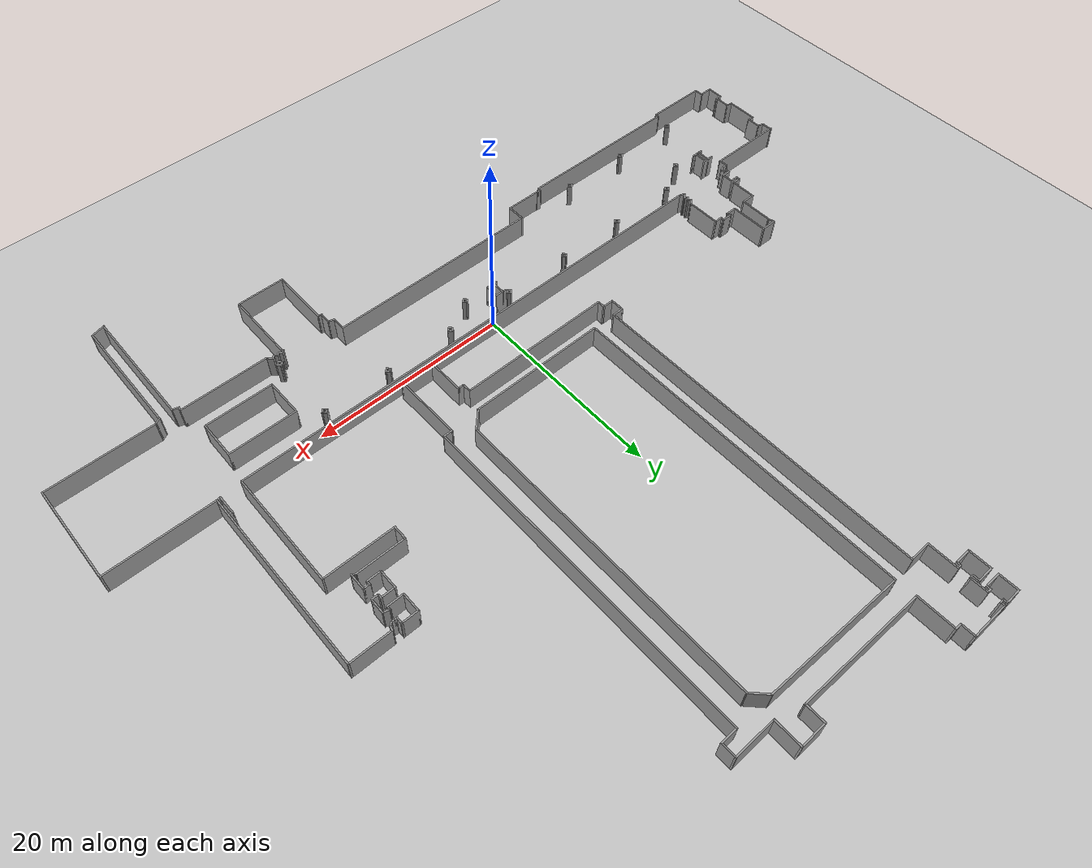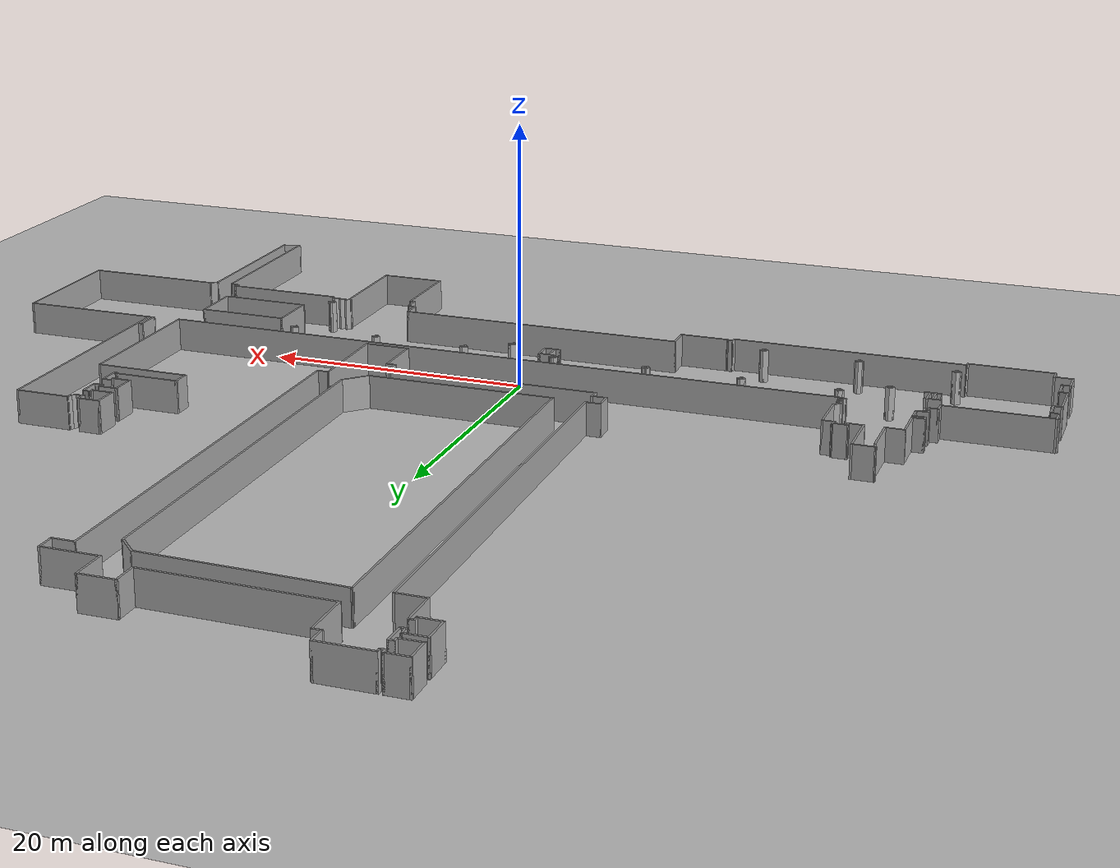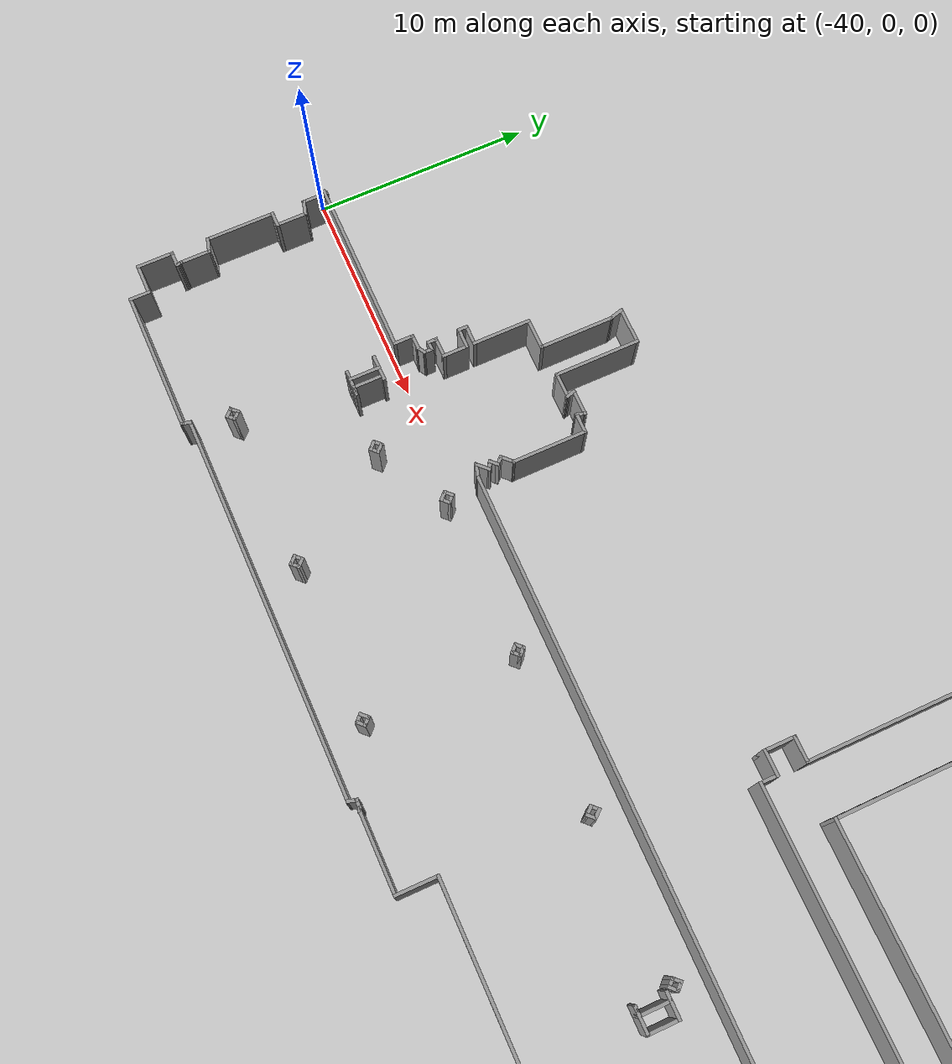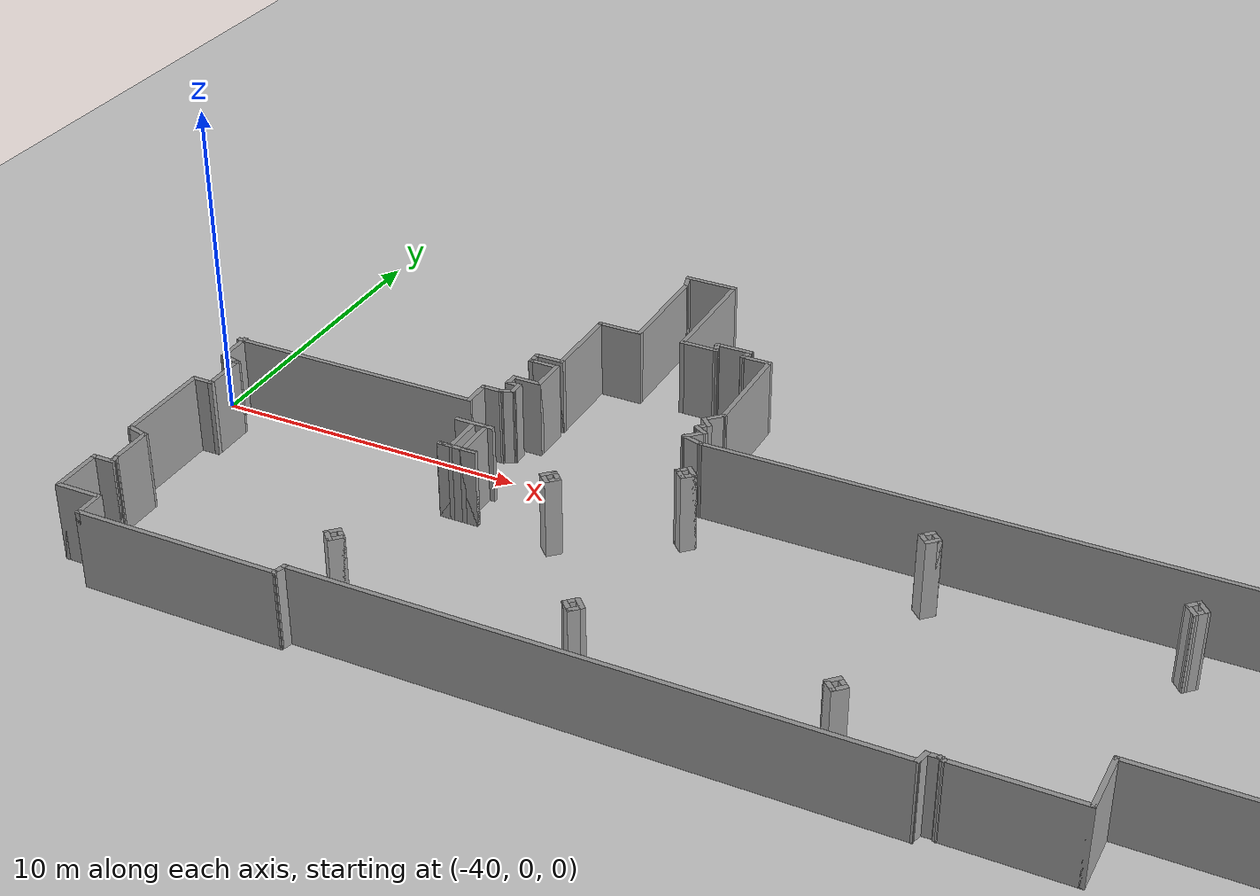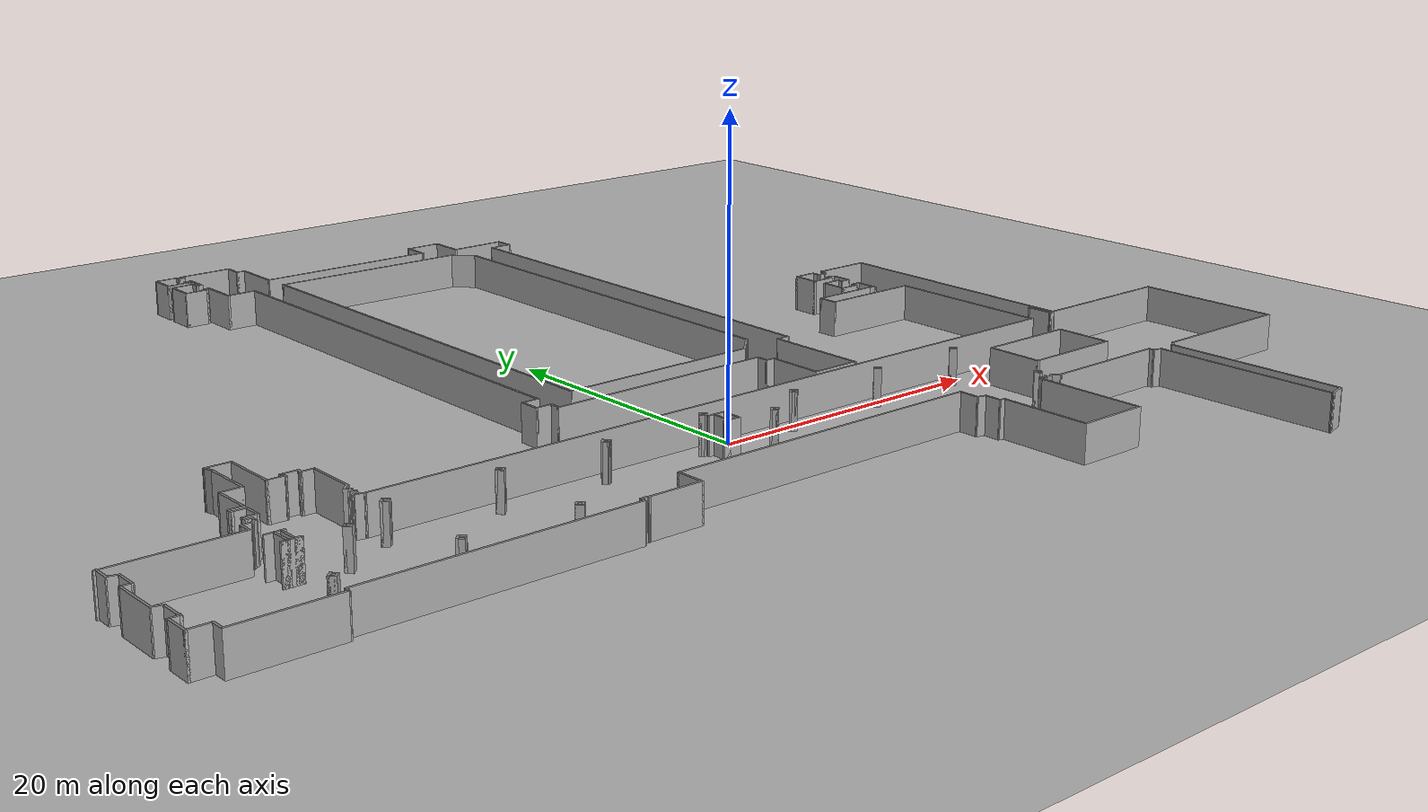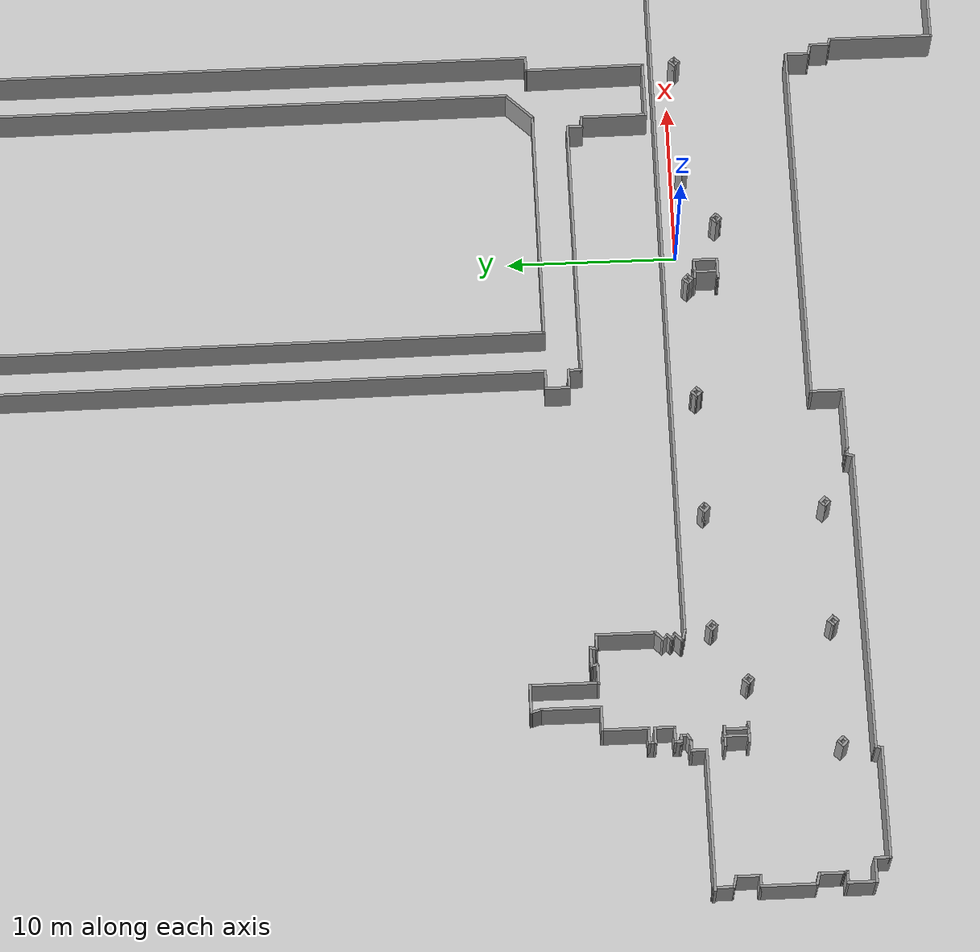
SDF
<sdf version="1.6">
 <world name="default">
  <light name="sun" type="directional">
   <pose>0 0 10 0 -0 0</pose>
   <diffuse>0.8 0.8 0.8 1</diffuse>
   <specular>0.2 0.2 0.2 1</specular>
   <attenuation>
    <range>1000</range>
    <constant>0.9</constant>
    <linear>0.01</linear>
    <quadratic>0.001</quadratic>
   </attenuation>
   <direction>-0.5 0.1 -0.9</direction>
  </light>
  <model name="ground_plane">
   <static>1</static>
   <link name="link">
    <collision name="collision">
     <geometry><plane><normal>0 0 1</normal><size>100 100</size></plane></geometry>
     <surface><friction><ode><mu>100</mu><mu2>50</mu2></ode></friction></surface>
    </collision>
    <visual name="visual">
     <cast_shadows>0</cast_shadows>
     <geometry><plane><normal>0 0 1</normal><size>100 100</size></plane></geometry>
     <material>
      <script><uri>file://media/materials/scripts/gazebo.material</uri><name>Gazebo/Grey</name></script>
     </material>
    </visual>
   </link>
  </model>
  <gravity>0 0 -9.8</gravity>
  <magnetic_field>6e-06 2.3e-05 -4.2e-05</magnetic_field>
  <atmosphere type="adiabatic"/>
  <physics name="default_physics" default="0" type="ode">
   <max_step_size>0.001</max_step_size>
   <real_time_factor>1</real_time_factor>
   <real_time_update_rate>1000</real_time_update_rate>
  </physics>
  <scene><ambient>0.4 0.4 0.4 1</ambient><background>0.7 0.7 0.7 1</background><shadows>1</shadows></scene>
  <audio><device>default</device></audio>
  <spherical_coordinates>
   <surface_model>EARTH_WGS84</surface_model>
   <latitude_deg>0</latitude_deg>
   <longitude_deg>0</longitude_deg>
   <elevation>0</elevation>
   <heading_deg>0</heading_deg>
  </spherical_coordinates>
  <model name="301_7f_1">
   <pose>1.02031 25.2413 0 0 0 -3.13556</pose>
   <link name="Wall_0">
    <collision name="Wall_0_Collision">
     <geometry><box><size>3.5 0.15 2.5</size></box></geometry>
     <pose>0 0 1.25 0 -0 0</pose>
    </collision>
    <visual name="Wall_0_Visual">
     <pose>0 0 1.25 0 -0 0</pose>
     <geometry><box><size>3.5 0.15 2.5</size></box></geometry>
     <material>
      <script><uri>file://media/materials/scripts/gazebo.material</uri><name>Gazebo/Grey</name></script>
      <ambient>1 1 1 1</ambient>
     </material>
     <meta><layer>0</layer></meta>
    </visual>
    <pose>-9.01493 23.8758 0 0 -0 0</pose>
   </link>
   <link name="Wall_1">
    <collision name="Wall_1_Collision">
     <geometry><box><size>4 0.15 2.5</size></box></geometry>
     <pose>0 0 1.25 0 -0 0</pose>
    </collision>
    <visual name="Wall_1_Visual">
     <pose>0 0 1.25 0 -0 0</pose>
     <geometry><box><size>4 0.15 2.5</size></box></geometry>
     <material>
      <script><uri>file://media/materials/scripts/gazebo.material</uri><name>Gazebo/Grey</name></script>
      <ambient>1 1 1 1</ambient>
     </material>
     <meta><layer>0</layer></meta>
    </visual>
    <pose>-7.33993 21.9508 0 0 -0 -1.5708</pose>
   </link>
   <link name="Wall_10">
    <collision name="Wall_10_Collision">
     <geometry><box><size>34 0.15 2.5</size></box></geometry>
     <pose>0 0 1.25 0 -0 0</pose>
    </collision>
    <visual name="Wall_10_Visual">
     <pose>0 0 1.25 0 -0 0</pose>
     <geometry><box><size>34 0.15 2.5</size></box></geometry>
     <material>
      <script><uri>file://media/materials/scripts/gazebo.material</uri><name>Gazebo/Grey</name></script>
      <ambient>1 1 1 1</ambient>
     </material>
     <meta><layer>0</layer></meta>
    </visual>
    <pose>9.09486 0.148677 0 0 -0 -1.5708</pose>
   </link>
   <link name="Wall_12">
    <collision name="Wall_12_Collision">
     <geometry><box><size>2.25 0.15 2.5</size></box></geometry>
     <pose>0 0 1.25 0 -0 0</pose>
    </collision>
    <visual name="Wall_12_Visual">
     <pose>0 0 1.25 0 -0 0</pose>
     <geometry><box><size>2.25 0.15 2.5</size></box></geometry>
     <material>
      <script><uri>file://media/materials/scripts/gazebo.material</uri><name>Gazebo/Grey</name></script>
      <ambient>1 1 1 1</ambient>
     </material>
     <meta><layer>0</layer></meta>
    </visual>
    <pose>10.1449 -16.7763 0 0 -0 0</pose>
   </link>
   <link name="Wall_13">
    <collision name="Wall_13_Collision">
     <geometry><box><size>3 0.15 2.5</size></box></geometry>
     <pose>0 0 1.25 0 -0 0</pose>
    </collision>
    <visual name="Wall_13_Visual">
     <pose>0 0 1.25 0 -0 0</pose>
     <geometry><box><size>3 0.15 2.5</size></box></geometry>
     <material>
      <script><uri>file://media/materials/scripts/gazebo.material</uri><name>Gazebo/Grey</name></script>
      <ambient>1 1 1 1</ambient>
     </material>
     <meta><layer>0</layer></meta>
    </visual>
    <pose>11.1949 -18.2013 0 0 -0 -1.5708</pose>
   </link>
   <link name="Wall_14">
    <collision name="Wall_14_Collision">
     <geometry><box><size>0.5 0.15 2.5</size></box></geometry>
     <pose>0 0 1.25 0 -0 0</pose>
    </collision>
    <visual name="Wall_14_Visual">
     <pose>0 0 1.25 0 -0 0</pose>
     <geometry><box><size>0.5 0.15 2.5</size></box></geometry>
     <material>
      <script><uri>file://media/materials/scripts/gazebo.material</uri><name>Gazebo/Grey</name></script>
      <ambient>1 1 1 1</ambient>
     </material>
     <meta><layer>0</layer></meta>
    </visual>
    <pose>11.3699 -19.6263 0 0 -0 0</pose>
   </link>
   <link name="Wall_15">
    <collision name="Wall_15_Collision">
     <geometry><box><size>0.5 0.15 2.5</size></box></geometry>
     <pose>0 0 1.25 0 -0 0</pose>
    </collision>
    <visual name="Wall_15_Visual">
     <pose>0 0 1.25 0 -0 0</pose>
     <geometry><box><size>0.5 0.15 2.5</size></box></geometry>
     <material>
      <script><uri>file://media/materials/scripts/gazebo.material</uri><name>Gazebo/Grey</name></script>
      <ambient>1 1 1 1</ambient>
     </material>
     <meta><layer>0</layer></meta>
    </visual>
    <pose>11.5449 -19.4513 0 0 -0 1.5708</pose>
   </link>
   <link name="Wall_16">
    <collision name="Wall_16_Collision">
     <geometry><box><size>1.75 0.15 2.5</size></box></geometry>
     <pose>0 0 1.25 0 -0 0</pose>
    </collision>
    <visual name="Wall_16_Visual">
     <pose>0 0 1.25 0 -0 0</pose>
     <geometry><box><size>1.75 0.15 2.5</size></box></geometry>
     <material>
      <script><uri>file://media/materials/scripts/gazebo.material</uri><name>Gazebo/Grey</name></script>
      <ambient>1 1 1 1</ambient>
     </material>
     <meta><layer>0</layer></meta>
    </visual>
    <pose>12.3449 -19.2763 0 0 -0 0</pose>
   </link>
   <link name="Wall_17">
    <collision name="Wall_17_Collision">
     <geometry><box><size>2.25 0.15 2.5</size></box></geometry>
     <pose>0 0 1.25 0 -0 0</pose>
    </collision>
    <visual name="Wall_17_Visual">
     <pose>0 0 1.25 0 -0 0</pose>
     <geometry><box><size>2.25 0.15 2.5</size></box></geometry>
     <material>
      <script><uri>file://media/materials/scripts/gazebo.material</uri><name>Gazebo/Grey</name></script>
      <ambient>1 1 1 1</ambient>
     </material>
     <meta><layer>0</layer></meta>
    </visual>
    <pose>13.1449 -20.3263 0 0 -0 -1.5708</pose>
   </link>
   <link name="Wall_18">
    <collision name="Wall_18_Collision">
     <geometry><box><size>1.75 0.15 2.5</size></box></geometry>
     <pose>0 0 1.25 0 -0 0</pose>
    </collision>
    <visual name="Wall_18_Visual">
     <pose>0 0 1.25 0 -0 0</pose>
     <geometry><box><size>1.75 0.15 2.5</size></box></geometry>
     <material>
      <script><uri>file://media/materials/scripts/gazebo.material</uri><name>Gazebo/Grey</name></script>
      <ambient>1 1 1 1</ambient>
     </material>
     <meta><layer>0</layer></meta>
    </visual>
    <pose>12.3449 -21.3763 0 0 -0 3.14159</pose>
   </link>
   <link name="Wall_19">
    <collision name="Wall_19_Collision">
     <geometry><box><size>0.75 0.15 2.5</size></box></geometry>
     <pose>0 0 1.25 0 -0 0</pose>
    </collision>
    <visual name="Wall_19_Visual">
     <pose>0 0 1.25 0 -0 0</pose>
     <geometry><box><size>0.75 0.15 2.5</size></box></geometry>
     <material>
      <script><uri>file://media/materials/scripts/gazebo.material</uri><name>Gazebo/Grey</name></script>
      <ambient>1 1 1 1</ambient>
     </material>
     <meta><layer>0</layer></meta>
    </visual>
    <pose>11.5449 -21.0763 0 0 -0 1.5708</pose>
   </link>
   <link name="Wall_2">
    <collision name="Wall_2_Collision">
     <geometry><box><size>0.75 0.15 2.5</size></box></geometry>
     <pose>0 0 1.25 0 -0 0</pose>
    </collision>
    <visual name="Wall_2_Visual">
     <pose>0 0 1.25 0 -0 0</pose>
     <geometry><box><size>0.75 0.15 2.5</size></box></geometry>
     <material>
      <script><uri>file://media/materials/scripts/gazebo.material</uri><name>Gazebo/Grey</name></script>
      <ambient>1 1 1 1</ambient>
     </material>
     <meta><layer>0</layer></meta>
    </visual>
    <pose>-7.03993 20.0258 0 0 -0 0</pose>
   </link>
   <link name="Wall_20">
    <collision name="Wall_20_Collision">
     <geometry><box><size>0.5 0.15 2.5</size></box></geometry>
     <pose>0 0 1.25 0 -0 0</pose>
    </collision>
    <visual name="Wall_20_Visual">
     <pose>0 0 1.25 0 -0 0</pose>
     <geometry><box><size>0.5 0.15 2.5</size></box></geometry>
     <material>
      <script><uri>file://media/materials/scripts/gazebo.material</uri><name>Gazebo/Grey</name></script>
      <ambient>1 1 1 1</ambient>
     </material>
     <meta><layer>0</layer></meta>
    </visual>
    <pose>11.3699 -20.7763 0 0 -0 3.14159</pose>
   </link>
   <link name="Wall_21">
    <collision name="Wall_21_Collision">
     <geometry><box><size>1.75 0.15 2.5</size></box></geometry>
     <pose>0 0 1.25 0 -0 0</pose>
    </collision>
    <visual name="Wall_21_Visual">
     <pose>0 0 1.25 0 -0 0</pose>
     <geometry><box><size>1.75 0.15 2.5</size></box></geometry>
     <material>
      <script><uri>file://media/materials/scripts/gazebo.material</uri><name>Gazebo/Grey</name></script>
      <ambient>1 1 1 1</ambient>
     </material>
     <meta><layer>0</layer></meta>
    </visual>
    <pose>11.1949 -21.5763 0 0 -0 -1.5708</pose>
   </link>
   <link name="Wall_22">
    <collision name="Wall_22_Collision">
     <geometry><box><size>0.5 0.15 2.5</size></box></geometry>
     <pose>0 0 1.25 0 -0 0</pose>
    </collision>
    <visual name="Wall_22_Visual">
     <pose>0 0 1.25 0 -0 0</pose>
     <geometry><box><size>0.5 0.15 2.5</size></box></geometry>
     <material>
      <script><uri>file://media/materials/scripts/gazebo.material</uri><name>Gazebo/Grey</name></script>
      <ambient>1 1 1 1</ambient>
     </material>
     <meta><layer>0</layer></meta>
    </visual>
    <pose>11.3699 -22.3763 0 0 -0 0</pose>
   </link>
   <link name="Wall_23">
    <collision name="Wall_23_Collision">
     <geometry><box><size>0.5 0.15 2.5</size></box></geometry>
     <pose>0 0 1.25 0 -0 0</pose>
    </collision>
    <visual name="Wall_23_Visual">
     <pose>0 0 1.25 0 -0 0</pose>
     <geometry><box><size>0.5 0.15 2.5</size></box></geometry>
     <material>
      <script><uri>file://media/materials/scripts/gazebo.material</uri><name>Gazebo/Grey</name></script>
      <ambient>1 1 1 1</ambient>
     </material>
     <meta><layer>0</layer></meta>
    </visual>
    <pose>11.5449 -22.2013 0 0 -0 1.5708</pose>
   </link>
   <link name="Wall_24">
    <collision name="Wall_24_Collision">
     <geometry><box><size>1.75 0.15 2.5</size></box></geometry>
     <pose>0 0 1.25 0 -0 0</pose>
    </collision>
    <visual name="Wall_24_Visual">
     <pose>0 0 1.25 0 -0 0</pose>
     <geometry><box><size>1.75 0.15 2.5</size></box></geometry>
     <material>
      <script><uri>file://media/materials/scripts/gazebo.material</uri><name>Gazebo/Grey</name></script>
      <ambient>1 1 1 1</ambient>
     </material>
     <meta><layer>0</layer></meta>
    </visual>
    <pose>12.3449 -22.0263 0 0 -0 0</pose>
   </link>
   <link name="Wall_25">
    <collision name="Wall_25_Collision">
     <geometry><box><size>2 0.15 2.5</size></box></geometry>
     <pose>0 0 1.25 0 -0 0</pose>
    </collision>
    <visual name="Wall_25_Visual">
     <pose>0 0 1.25 0 -0 0</pose>
     <geometry><box><size>2 0.15 2.5</size></box></geometry>
     <material>
      <script><uri>file://media/materials/scripts/gazebo.material</uri><name>Gazebo/Grey</name></script>
      <ambient>1 1 1 1</ambient>
     </material>
     <meta><layer>0</layer></meta>
    </visual>
    <pose>13.1449 -22.9513 0 0 -0 -1.5708</pose>
   </link>
   <link name="Wall_26">
    <collision name="Wall_26_Collision">
     <geometry><box><size>1.75 0.15 2.5</size></box></geometry>
     <pose>0 0 1.25 0 -0 0</pose>
    </collision>
    <visual name="Wall_26_Visual">
     <pose>0 0 1.25 0 -0 0</pose>
     <geometry><box><size>1.75 0.15 2.5</size></box></geometry>
     <material>
      <script><uri>file://media/materials/scripts/gazebo.material</uri><name>Gazebo/Grey</name></script>
      <ambient>1 1 1 1</ambient>
     </material>
     <meta><layer>0</layer></meta>
    </visual>
    <pose>12.3449 -23.8763 0 0 -0 3.14159</pose>
   </link>
   <link name="Wall_27">
    <collision name="Wall_27_Collision">
     <geometry><box><size>0.5 0.15 2.5</size></box></geometry>
     <pose>0 0 1.25 0 -0 0</pose>
    </collision>
    <visual name="Wall_27_Visual">
     <pose>0 0 1.25 0 -0 0</pose>
     <geometry><box><size>0.5 0.15 2.5</size></box></geometry>
     <material>
      <script><uri>file://media/materials/scripts/gazebo.material</uri><name>Gazebo/Grey</name></script>
      <ambient>1 1 1 1</ambient>
     </material>
     <meta><layer>0</layer></meta>
    </visual>
    <pose>11.5449 -23.7013 0 0 -0 1.5708</pose>
   </link>
   <link name="Wall_28">
    <collision name="Wall_28_Collision">
     <geometry><box><size>0.5 0.15 2.5</size></box></geometry>
     <pose>0 0 1.25 0 -0 0</pose>
    </collision>
    <visual name="Wall_28_Visual">
     <pose>0 0 1.25 0 -0 0</pose>
     <geometry><box><size>0.5 0.15 2.5</size></box></geometry>
     <material>
      <script><uri>file://media/materials/scripts/gazebo.material</uri><name>Gazebo/Grey</name></script>
      <ambient>1 1 1 1</ambient>
     </material>
     <meta><layer>0</layer></meta>
    </visual>
    <pose>11.3699 -23.5263 0 0 -0 3.14159</pose>
   </link>
   <link name="Wall_29">
    <collision name="Wall_29_Collision">
     <geometry><box><size>0.5 0.15 2.5</size></box></geometry>
     <pose>0 0 1.25 0 -0 0</pose>
    </collision>
    <visual name="Wall_29_Visual">
     <pose>0 0 1.25 0 -0 0</pose>
     <geometry><box><size>0.5 0.15 2.5</size></box></geometry>
     <material>
      <script><uri>file://media/materials/scripts/gazebo.material</uri><name>Gazebo/Grey</name></script>
      <ambient>1 1 1 1</ambient>
     </material>
     <meta><layer>0</layer></meta>
    </visual>
    <pose>11.1949 -23.7013 0 0 -0 -1.5708</pose>
   </link>
   <link name="Wall_3">
    <collision name="Wall_3_Collision">
     <geometry><box><size>1 0.15 2.5</size></box></geometry>
     <pose>0 0 1.25 0 -0 0</pose>
    </collision>
    <visual name="Wall_3_Visual">
     <pose>0 0 1.25 0 -0 0</pose>
     <geometry><box><size>1 0.15 2.5</size></box></geometry>
     <material>
      <script><uri>file://media/materials/scripts/gazebo.material</uri><name>Gazebo/Grey</name></script>
      <ambient>1 1 1 1</ambient>
     </material>
     <meta><layer>0</layer></meta>
    </visual>
    <pose>-6.73993 19.6008 0 0 -0 -1.5708</pose>
   </link>
   <link name="Wall_30">
    <collision name="Wall_30_Collision">
     <geometry><box><size>4 0.15 2.5</size></box></geometry>
     <pose>0 0 1.25 0 -0 0</pose>
    </collision>
    <visual name="Wall_30_Visual">
     <pose>0 0 1.25 0 -0 0</pose>
     <geometry><box><size>4 0.15 2.5</size></box></geometry>
     <material>
      <script><uri>file://media/materials/scripts/gazebo.material</uri><name>Gazebo/Grey</name></script>
      <ambient>1 1 1 1</ambient>
     </material>
     <meta><layer>0</layer></meta>
    </visual>
    <pose>9.26986 -23.8763 0 0 -0 3.14159</pose>
   </link>
   <link name="Wall_31">
    <collision name="Wall_31_Collision">
     <geometry><box><size>1.5 0.15 2.5</size></box></geometry>
     <pose>0 0 1.25 0 -0 0</pose>
    </collision>
    <visual name="Wall_31_Visual">
     <pose>0 0 1.25 0 -0 0</pose>
     <geometry><box><size>1.5 0.15 2.5</size></box></geometry>
     <material>
      <script><uri>file://media/materials/scripts/gazebo.material</uri><name>Gazebo/Grey</name></script>
      <ambient>1 1 1 1</ambient>
     </material>
     <meta><layer>0</layer></meta>
    </visual>
    <pose>7.34486 -23.2013 0 0 -0 1.5708</pose>
   </link>
   <link name="Wall_32">
    <collision name="Wall_32_Collision">
     <geometry><box><size>0.75 0.15 2.5</size></box></geometry>
     <pose>0 0 1.25 0 -0 0</pose>
    </collision>
    <visual name="Wall_32_Visual">
     <pose>0 0 1.25 0 -0 0</pose>
     <geometry><box><size>0.75 0.15 2.5</size></box></geometry>
     <material>
      <script><uri>file://media/materials/scripts/gazebo.material</uri><name>Gazebo/Grey</name></script>
      <ambient>1 1 1 1</ambient>
     </material>
     <meta><layer>0</layer></meta>
    </visual>
    <pose>7.04486 -22.5263 0 0 -0 3.14159</pose>
   </link>
   <link name="Wall_33">
    <collision name="Wall_33_Collision">
     <geometry><box><size>3.75 0.15 2.5</size></box></geometry>
     <pose>0 0 1.25 0 -0 0</pose>
    </collision>
    <visual name="Wall_33_Visual">
     <pose>0 0 1.25 0 -0 0</pose>
     <geometry><box><size>3.75 0.15 2.5</size></box></geometry>
     <material>
      <script><uri>file://media/materials/scripts/gazebo.material</uri><name>Gazebo/Grey</name></script>
      <ambient>1 1 1 1</ambient>
     </material>
     <meta><layer>0</layer></meta>
    </visual>
    <pose>6.74486 -20.7263 0 0 -0 1.5708</pose>
   </link>
   <link name="Wall_34">
    <collision name="Wall_34_Collision">
     <geometry><box><size>13.3413 0.15 2.5</size></box></geometry>
     <pose>0 0 1.25 0 -0 0</pose>
    </collision>
    <visual name="Wall_34_Visual">
     <pose>0 0 1.25 0 -0 0</pose>
     <geometry><box><size>13.3413 0.15 2.5</size></box></geometry>
     <material>
      <script><uri>file://media/materials/scripts/gazebo.material</uri><name>Gazebo/Grey</name></script>
      <ambient>1 1 1 1</ambient>
     </material>
     <meta><layer>0</layer></meta>
    </visual>
    <pose>0.15 -18.8254 0 0 -0 3.12629</pose>
   </link>
   <link name="Wall_36">
    <collision name="Wall_36_Collision">
     <geometry><box><size>2 0.15 2.5</size></box></geometry>
     <pose>0 0 1.25 0 -0 0</pose>
    </collision>
    <visual name="Wall_36_Visual">
     <pose>0 0 1.25 0 -0 0</pose>
     <geometry><box><size>2 0.15 2.5</size></box></geometry>
     <material>
      <script><uri>file://media/materials/scripts/gazebo.material</uri><name>Gazebo/Grey</name></script>
      <ambient>1 1 1 1</ambient>
     </material>
     <meta><layer>0</layer></meta>
    </visual>
    <pose>-6.44486 -19.6495 0 0 -0 -1.5708</pose>
   </link>
   <link name="Wall_37">
    <collision name="Wall_37_Collision">
     <geometry><box><size>2.75 0.15 2.5</size></box></geometry>
     <pose>0 0 1.25 0 -0 0</pose>
    </collision>
    <visual name="Wall_37_Visual">
     <pose>0 0 1.25 0 -0 0</pose>
     <geometry><box><size>2.75 0.15 2.5</size></box></geometry>
     <material>
      <script><uri>file://media/materials/scripts/gazebo.material</uri><name>Gazebo/Grey</name></script>
      <ambient>1 1 1 1</ambient>
     </material>
     <meta><layer>0</layer></meta>
    </visual>
    <pose>-7.74486 -20.5745 0 0 -0 3.14159</pose>
   </link>
   <link name="Wall_38">
    <collision name="Wall_38_Collision">
     <geometry><box><size>2.75 0.15 2.5</size></box></geometry>
     <pose>0 0 1.25 0 -0 0</pose>
    </collision>
    <visual name="Wall_38_Visual">
     <pose>0 0 1.25 0 -0 0</pose>
     <geometry><box><size>2.75 0.15 2.5</size></box></geometry>
     <material>
      <script><uri>file://media/materials/scripts/gazebo.material</uri><name>Gazebo/Grey</name></script>
      <ambient>1 1 1 1</ambient>
     </material>
     <meta><layer>0</layer></meta>
    </visual>
    <pose>-9.04486 -19.2745 0 0 -0 1.5708</pose>
   </link>
   <link name="Wall_39">
    <collision name="Wall_39_Collision">
     <geometry><box><size>4.25 0.15 2.5</size></box></geometry>
     <pose>0 0 1.25 0 -0 0</pose>
    </collision>
    <visual name="Wall_39_Visual">
     <pose>0 0 1.25 0 -0 0</pose>
     <geometry><box><size>4.25 0.15 2.5</size></box></geometry>
     <material>
      <script><uri>file://media/materials/scripts/gazebo.material</uri><name>Gazebo/Grey</name></script>
      <ambient>1 1 1 1</ambient>
     </material>
     <meta><layer>0</layer></meta>
    </visual>
    <pose>-11.0949 -17.9745 0 0 -0 3.14159</pose>
   </link>
   <link name="Wall_4">
    <collision name="Wall_4_Collision">
     <geometry><box><size>16 0.15 2.5</size></box></geometry>
     <pose>0 0 1.25 0 -0 0</pose>
    </collision>
    <visual name="Wall_4_Visual">
     <pose>0 0 1.25 0 -0 0</pose>
     <geometry><box><size>16 0.15 2.5</size></box></geometry>
     <material>
      <script><uri>file://media/materials/scripts/gazebo.material</uri><name>Gazebo/Grey</name></script>
      <ambient>1 1 1 1</ambient>
     </material>
     <meta><layer>0</layer></meta>
    </visual>
    <pose>1.18507 19.1758 0 0 -0 0</pose>
   </link>
   <link name="Wall_40">
    <collision name="Wall_40_Collision">
     <geometry><box><size>1.5 0.15 2.5</size></box></geometry>
     <pose>0 0 1.25 0 -0 0</pose>
    </collision>
    <visual name="Wall_40_Visual">
     <pose>0 0 1.25 0 -0 0</pose>
     <geometry><box><size>1.5 0.15 2.5</size></box></geometry>
     <material>
      <script><uri>file://media/materials/scripts/gazebo.material</uri><name>Gazebo/Grey</name></script>
      <ambient>1 1 1 1</ambient>
     </material>
     <meta><layer>0</layer></meta>
    </visual>
    <pose>-13.1449 -17.2995 0 0 -0 1.5708</pose>
   </link>
   <link name="Wall_41">
    <collision name="Wall_41_Collision">
     <geometry><box><size>1.75 0.15 2.5</size></box></geometry>
     <pose>0 0 1.25 0 -0 0</pose>
    </collision>
    <visual name="Wall_41_Visual">
     <pose>0 0 1.25 0 -0 0</pose>
     <geometry><box><size>1.75 0.15 2.5</size></box></geometry>
     <material>
      <script><uri>file://media/materials/scripts/gazebo.material</uri><name>Gazebo/Grey</name></script>
      <ambient>1 1 1 1</ambient>
     </material>
     <meta><layer>0</layer></meta>
    </visual>
    <pose>-12.3449 -16.6245 0 0 -0 0</pose>
   </link>
   <link name="Wall_42">
    <collision name="Wall_42_Collision">
     <geometry><box><size>33.6472 0.15 2.5</size></box></geometry>
     <pose>0 0 1.25 0 -0 0</pose>
    </collision>
    <visual name="Wall_42_Visual">
     <pose>0 0 1.25 0 -0 0</pose>
     <geometry><box><size>33.6472 0.15 2.5</size></box></geometry>
     <material>
      <script><uri>file://media/materials/scripts/gazebo.material</uri><name>Gazebo/Grey</name></script>
      <ambient>1 1 1 1</ambient>
     </material>
     <meta><layer>0</layer></meta>
    </visual>
    <pose>-11.5163 0.124114 0 0 -0 1.56909</pose>
   </link>
   <link name="Wall_44">
    <collision name="Wall_44_Collision">
     <geometry><box><size>1 0.15 2.5</size></box></geometry>
     <pose>0 0 1.25 0 -0 0</pose>
    </collision>
    <visual name="Wall_44_Visual">
     <pose>0 0 1.25 0 -0 0</pose>
     <geometry><box><size>1 0.15 2.5</size></box></geometry>
     <material>
      <script><uri>file://media/materials/scripts/gazebo.material</uri><name>Gazebo/Grey</name></script>
      <ambient>1 1 1 1</ambient>
     </material>
     <meta><layer>0</layer></meta>
    </visual>
    <pose>-11.0627 16.8727 0 0 -0 0</pose>
   </link>
   <link name="Wall_46">
    <collision name="Wall_46_Collision">
     <geometry><box><size>7.15327 0.15 2.5</size></box></geometry>
     <pose>0 0 1.25 0 -0 0</pose>
    </collision>
    <visual name="Wall_46_Visual">
     <pose>0 0 1.25 0 -0 0</pose>
     <geometry><box><size>7.15327 0.15 2.5</size></box></geometry>
     <material>
      <script><uri>file://media/materials/scripts/gazebo.material</uri><name>Gazebo/Grey</name></script>
      <ambient>1 1 1 1</ambient>
     </material>
     <meta><layer>0</layer></meta>
    </visual>
    <pose>-10.6638 20.3742 0 0 -0 1.57826</pose>
   </link>
   <link name="Wall_48">
    <collision name="Wall_48_Collision">
     <geometry><box><size>2.25 0.15 2.5</size></box></geometry>
     <pose>0 0 1.25 0 -0 0</pose>
    </collision>
    <visual name="Wall_48_Visual">
     <pose>0 0 1.25 0 -0 0</pose>
     <geometry><box><size>2.25 0.15 2.5</size></box></geometry>
     <material>
      <script><uri>file://media/materials/scripts/gazebo.material</uri><name>Gazebo/Grey</name></script>
      <ambient>1 1 1 1</ambient>
     </material>
     <meta><layer>0</layer></meta>
    </visual>
    <pose>-8.21429 16.3704 0 0 -0 0.785398</pose>
   </link>
   <link name="Wall_49">
    <collision name="Wall_49_Collision">
     <geometry><box><size>14.25 0.15 2.5</size></box></geometry>
     <pose>0 0 1.25 0 -0 0</pose>
    </collision>
    <visual name="Wall_49_Visual">
     <pose>0 0 1.25 0 -0 0</pose>
     <geometry><box><size>14.25 0.15 2.5</size></box></geometry>
     <material>
      <script><uri>file://media/materials/scripts/gazebo.material</uri><name>Gazebo/Grey</name></script>
      <ambient>1 1 1 1</ambient>
     </material>
     <meta><layer>0</layer></meta>
    </visual>
    <pose>-0.421827 17.1129 0 0 -0 0</pose>
   </link>
   <link name="Wall_5">
    <collision name="Wall_5_Collision">
     <geometry><box><size>0.902088 0.15 2.5</size></box></geometry>
     <pose>0 0 1.25 0 -0 0</pose>
    </collision>
    <visual name="Wall_5_Visual">
     <pose>0 0 1.25 0 -0 0</pose>
     <geometry><box><size>0.902088 0.15 2.5</size></box></geometry>
     <material>
      <script><uri>file://media/materials/scripts/gazebo.material</uri><name>Gazebo/Grey</name></script>
      <ambient>1 1 1 1</ambient>
     </material>
     <meta><layer>0</layer></meta>
    </visual>
    <pose>9.11007 18.7997 0 0 -0 -1.5708</pose>
   </link>
   <link name="Wall_50">
    <collision name="Wall_50_Collision">
     <geometry><box><size>34.25 0.15 2.5</size></box></geometry>
     <pose>0 0 1.25 0 -0 0</pose>
    </collision>
    <visual name="Wall_50_Visual">
     <pose>0 0 1.25 0 -0 0</pose>
     <geometry><box><size>34.25 0.15 2.5</size></box></geometry>
     <material>
      <script><uri>file://media/materials/scripts/gazebo.material</uri><name>Gazebo/Grey</name></script>
      <ambient>1 1 1 1</ambient>
     </material>
     <meta><layer>0</layer></meta>
    </visual>
    <pose>6.62817 0.062903 0 0 -0 -1.5708</pose>
   </link>
   <link name="Wall_52">
    <collision name="Wall_52_Collision">
     <geometry><box><size>14.4831 0.15 2.5</size></box></geometry>
     <pose>0 0 1.25 0 -0 0</pose>
    </collision>
    <visual name="Wall_52_Visual">
     <pose>0 0 1.25 0 -0 0</pose>
     <geometry><box><size>14.4831 0.15 2.5</size></box></geometry>
     <material>
      <script><uri>file://media/materials/scripts/gazebo.material</uri><name>Gazebo/Grey</name></script>
      <ambient>1 1 1 1</ambient>
     </material>
     <meta><layer>0</layer></meta>
    </visual>
    <pose>-0.536504 -16.8228 0 0 -0 3.11866</pose>
   </link>
   <link name="Wall_53">
    <collision name="Wall_53_Collision">
     <geometry><box><size>2 0.15 2.5</size></box></geometry>
     <pose>0 0 1.25 0 -0 0</pose>
    </collision>
    <visual name="Wall_53_Visual">
     <pose>0 0 1.25 0 -0 0</pose>
     <geometry><box><size>2 0.15 2.5</size></box></geometry>
     <material>
      <script><uri>file://media/materials/scripts/gazebo.material</uri><name>Gazebo/Grey</name></script>
      <ambient>1 1 1 1</ambient>
     </material>
     <meta><layer>0</layer></meta>
    </visual>
    <pose>-8.37459 -16.0044 0 0 -0 2.35619</pose>
   </link>
   <link name="Wall_55">
    <collision name="Wall_55_Collision">
     <geometry><box><size>31.0796 0.15 2.5</size></box></geometry>
     <pose>0 0 1.25 0 -0 0</pose>
    </collision>
    <visual name="Wall_55_Visual">
     <pose>0 0 1.25 0 -0 0</pose>
     <geometry><box><size>31.0796 0.15 2.5</size></box></geometry>
     <material>
      <script><uri>file://media/materials/scripts/gazebo.material</uri><name>Gazebo/Grey</name></script>
      <ambient>1 1 1 1</ambient>
     </material>
     <meta><layer>0</layer></meta>
    </visual>
    <pose>-9.01012 0.114477 0 0 -0 1.5696</pose>
   </link>
   <link name="Wall_6">
    <collision name="Wall_6_Collision">
     <geometry><box><size>1.25 0.15 2.5</size></box></geometry>
     <pose>0 0 1.25 0 -0 0</pose>
    </collision>
    <visual name="Wall_6_Visual">
     <pose>0 0 1.25 0 -0 0</pose>
     <geometry><box><size>1.25 0.15 2.5</size></box></geometry>
     <material>
      <script><uri>file://media/materials/scripts/gazebo.material</uri><name>Gazebo/Grey</name></script>
      <ambient>1 1 1 1</ambient>
     </material>
     <meta><layer>0</layer></meta>
    </visual>
    <pose>9.64486 18.4237 0 0 -0 0</pose>
   </link>
   <link name="Wall_8">
    <collision name="Wall_8_Collision">
     <geometry><box><size>1.5 0.15 2.5</size></box></geometry>
     <pose>0 0 1.25 0 -0 0</pose>
    </collision>
    <visual name="Wall_8_Visual">
     <pose>0 0 1.25 0 -0 0</pose>
     <geometry><box><size>1.5 0.15 2.5</size></box></geometry>
     <material>
      <script><uri>file://media/materials/scripts/gazebo.material</uri><name>Gazebo/Grey</name></script>
      <ambient>1 1 1 1</ambient>
     </material>
     <meta><layer>0</layer></meta>
    </visual>
    <pose>10.1949 17.7487 0 0 -0 -1.5708</pose>
   </link>
   <link name="Wall_9">
    <collision name="Wall_9_Collision">
     <geometry><box><size>1.25 0.15 2.5</size></box></geometry>
     <pose>0 0 1.25 0 -0 0</pose>
    </collision>
    <visual name="Wall_9_Visual">
     <pose>0 0 1.25 0 -0 0</pose>
     <geometry><box><size>1.25 0.15 2.5</size></box></geometry>
     <material>
      <script><uri>file://media/materials/scripts/gazebo.material</uri><name>Gazebo/Grey</name></script>
      <ambient>1 1 1 1</ambient>
     </material>
     <meta><layer>0</layer></meta>
    </visual>
    <pose>9.64486 17.0737 0 0 -0 3.14159</pose>
   </link>
   <static>1</static>
  </model>
  <model name="301_1f_2">
   <pose>0.932725 -1.08367 0 0 -0 0</pose>
   <link name="Wall_10">
    <collision name="Wall_10_Collision">
     <geometry><box><size>0.75 0.15 2.5</size></box></geometry>
     <pose>0 0 1.25 0 -0 0</pose>
    </collision>
    <visual name="Wall_10_Visual">
     <pose>0 0 1.25 0 -0 0</pose>
     <geometry><box><size>0.75 0.15 2.5</size></box></geometry>
     <material>
      <script><uri>file://media/materials/scripts/gazebo.material</uri><name>Gazebo/Grey</name></script>
      <ambient>1 1 1 1</ambient>
     </material>
     <meta><layer>0</layer></meta>
    </visual>
    <pose>-40.0631 -4.54955 0 0 -0 -0.261799</pose>
   </link>
   <link name="Wall_100">
    <collision name="Wall_100_Collision">
     <geometry><box><size>0.5 0.15 2.5</size></box></geometry>
     <pose>0 0 1.25 0 -0 0</pose>
    </collision>
    <visual name="Wall_100_Visual">
     <pose>0 0 1.25 0 -0 0</pose>
     <geometry><box><size>0.5 0.15 2.5</size></box></geometry>
     <material>
      <script><uri>file://media/materials/scripts/gazebo.material</uri><name>Gazebo/Grey</name></script>
      <ambient>1 1 1 1</ambient>
     </material>
     <meta><layer>0</layer></meta>
    </visual>
    <pose>-26.0943 7.19008 0 0 -0 1.309</pose>
   </link>
   <link name="Wall_101">
    <collision name="Wall_101_Collision">
     <geometry><box><size>1.25 0.15 2.5</size></box></geometry>
     <pose>0 0 1.25 0 -0 0</pose>
    </collision>
    <visual name="Wall_101_Visual">
     <pose>0 0 1.25 0 -0 0</pose>
     <geometry><box><size>1.25 0.15 2.5</size></box></geometry>
     <material>
      <script><uri>file://media/materials/scripts/gazebo.material</uri><name>Gazebo/Grey</name></script>
      <ambient>1 1 1 1</ambient>
     </material>
     <meta><layer>0</layer></meta>
    </visual>
    <pose>-26.599 7.35912 0 0 -0 3.14159</pose>
   </link>
   <link name="Wall_102">
    <collision name="Wall_102_Collision">
     <geometry><box><size>0.5 0.15 2.5</size></box></geometry>
     <pose>0 0 1.25 0 -0 0</pose>
    </collision>
    <visual name="Wall_102_Visual">
     <pose>0 0 1.25 0 -0 0</pose>
     <geometry><box><size>0.5 0.15 2.5</size></box></geometry>
     <material>
      <script><uri>file://media/materials/scripts/gazebo.material</uri><name>Gazebo/Grey</name></script>
      <ambient>1 1 1 1</ambient>
     </material>
     <meta><layer>0</layer></meta>
    </visual>
    <pose>-27.1037 7.19008 0 0 -0 -1.309</pose>
   </link>
   <link name="Wall_103">
    <collision name="Wall_103_Collision">
     <geometry><box><size>1.25 0.15 2.5</size></box></geometry>
     <pose>0 0 1.25 0 -0 0</pose>
    </collision>
    <visual name="Wall_103_Visual">
     <pose>0 0 1.25 0 -0 0</pose>
     <geometry><box><size>1.25 0.15 2.5</size></box></geometry>
     <material>
      <script><uri>file://media/materials/scripts/gazebo.material</uri><name>Gazebo/Grey</name></script>
      <ambient>1 1 1 1</ambient>
     </material>
     <meta><layer>0</layer></meta>
    </visual>
    <pose>-27.6084 7.02104 0 0 -0 3.14159</pose>
   </link>
   <link name="Wall_104">
    <collision name="Wall_104_Collision">
     <geometry><box><size>4 0.15 2.5</size></box></geometry>
     <pose>0 0 1.25 0 -0 0</pose>
    </collision>
    <visual name="Wall_104_Visual">
     <pose>0 0 1.25 0 -0 0</pose>
     <geometry><box><size>4 0.15 2.5</size></box></geometry>
     <material>
      <script><uri>file://media/materials/scripts/gazebo.material</uri><name>Gazebo/Grey</name></script>
      <ambient>1 1 1 1</ambient>
     </material>
     <meta><layer>0</layer></meta>
    </visual>
    <pose>-28.1584 8.94604 0 0 -0 1.5708</pose>
   </link>
   <link name="Wall_105">
    <collision name="Wall_105_Collision">
     <geometry><box><size>1.75 0.15 2.5</size></box></geometry>
     <pose>0 0 1.25 0 -0 0</pose>
    </collision>
    <visual name="Wall_105_Visual">
     <pose>0 0 1.25 0 -0 0</pose>
     <geometry><box><size>1.75 0.15 2.5</size></box></geometry>
     <material>
      <script><uri>file://media/materials/scripts/gazebo.material</uri><name>Gazebo/Grey</name></script>
      <ambient>1 1 1 1</ambient>
     </material>
     <meta><layer>0</layer></meta>
    </visual>
    <pose>-28.9584 10.871 0 0 -0 3.14159</pose>
   </link>
   <link name="Wall_106">
    <collision name="Wall_106_Collision">
     <geometry><box><size>0.75 0.15 2.5</size></box></geometry>
     <pose>0 0 1.25 0 -0 0</pose>
    </collision>
    <visual name="Wall_106_Visual">
     <pose>0 0 1.25 0 -0 0</pose>
     <geometry><box><size>0.75 0.15 2.5</size></box></geometry>
     <material>
      <script><uri>file://media/materials/scripts/gazebo.material</uri><name>Gazebo/Grey</name></script>
      <ambient>1 1 1 1</ambient>
     </material>
     <meta><layer>0</layer></meta>
    </visual>
    <pose>-29.6807 10.5813 0 0 -0 -1.309</pose>
   </link>
   <link name="Wall_107">
    <collision name="Wall_107_Collision">
     <geometry><box><size>3.5 0.15 2.5</size></box></geometry>
     <pose>0 0 1.25 0 -0 0</pose>
    </collision>
    <visual name="Wall_107_Visual">
     <pose>0 0 1.25 0 -0 0</pose>
     <geometry><box><size>3.5 0.15 2.5</size></box></geometry>
     <material>
      <script><uri>file://media/materials/scripts/gazebo.material</uri><name>Gazebo/Grey</name></script>
      <ambient>1 1 1 1</ambient>
     </material>
     <meta><layer>0</layer></meta>
    </visual>
    <pose>-29.6031 8.61649 0 0 -0 -1.5708</pose>
   </link>
   <link name="Wall_108">
    <collision name="Wall_108_Collision">
     <geometry><box><size>1.5 0.15 2.5</size></box></geometry>
     <pose>0 0 1.25 0 -0 0</pose>
    </collision>
    <visual name="Wall_108_Visual">
     <pose>0 0 1.25 0 -0 0</pose>
     <geometry><box><size>1.5 0.15 2.5</size></box></geometry>
     <material>
      <script><uri>file://media/materials/scripts/gazebo.material</uri><name>Gazebo/Grey</name></script>
      <ambient>1 1 1 1</ambient>
     </material>
     <meta><layer>0</layer></meta>
    </visual>
    <pose>-30.2781 6.94149 0 0 -0 3.14159</pose>
   </link>
   <link name="Wall_109">
    <collision name="Wall_109_Collision">
     <geometry><box><size>2.75 0.15 2.5</size></box></geometry>
     <pose>0 0 1.25 0 -0 0</pose>
    </collision>
    <visual name="Wall_109_Visual">
     <pose>0 0 1.25 0 -0 0</pose>
     <geometry><box><size>2.75 0.15 2.5</size></box></geometry>
     <material>
      <script><uri>file://media/materials/scripts/gazebo.material</uri><name>Gazebo/Grey</name></script>
      <ambient>1 1 1 1</ambient>
     </material>
     <meta><layer>0</layer></meta>
    </visual>
    <pose>-30.9531 5.64149 0 0 -0 -1.5708</pose>
   </link>
   <link name="Wall_11">
    <collision name="Wall_11_Collision">
     <geometry><box><size>1.5 0.15 2.5</size></box></geometry>
     <pose>0 0 1.25 0 -0 0</pose>
    </collision>
    <visual name="Wall_11_Visual">
     <pose>0 0 1.25 0 -0 0</pose>
     <geometry><box><size>1.5 0.15 2.5</size></box></geometry>
     <material>
      <script><uri>file://media/materials/scripts/gazebo.material</uri><name>Gazebo/Grey</name></script>
      <ambient>1 1 1 1</ambient>
     </material>
     <meta><layer>0</layer></meta>
    </visual>
    <pose>-39.7734 -5.30219 0 0 -0 -1.5708</pose>
   </link>
   <link name="Wall_110">
    <collision name="Wall_110_Collision">
     <geometry><box><size>1 0.15 2.5</size></box></geometry>
     <pose>0 0 1.25 0 -0 0</pose>
    </collision>
    <visual name="Wall_110_Visual">
     <pose>0 0 1.25 0 -0 0</pose>
     <geometry><box><size>1 0.15 2.5</size></box></geometry>
     <material>
      <script><uri>file://media/materials/scripts/gazebo.material</uri><name>Gazebo/Grey</name></script>
      <ambient>1 1 1 1</ambient>
     </material>
     <meta><layer>0</layer></meta>
    </visual>
    <pose>-31.3781 4.34149 0 0 -0 3.14159</pose>
   </link>
   <link name="Wall_111">
    <collision name="Wall_111_Collision">
     <geometry><box><size>0.5 0.15 2.5</size></box></geometry>
     <pose>0 0 1.25 0 -0 0</pose>
    </collision>
    <visual name="Wall_111_Visual">
     <pose>0 0 1.25 0 -0 0</pose>
     <geometry><box><size>0.5 0.15 2.5</size></box></geometry>
     <material>
      <script><uri>file://media/materials/scripts/gazebo.material</uri><name>Gazebo/Grey</name></script>
      <ambient>1 1 1 1</ambient>
     </material>
     <meta><layer>0</layer></meta>
    </visual>
    <pose>-31.8031 4.16649 0 0 -0 -1.5708</pose>
   </link>
   <link name="Wall_112">
    <collision name="Wall_112_Collision">
     <geometry><box><size>1 0.15 2.5</size></box></geometry>
     <pose>0 0 1.25 0 -0 0</pose>
    </collision>
    <visual name="Wall_112_Visual">
     <pose>0 0 1.25 0 -0 0</pose>
     <geometry><box><size>1 0.15 2.5</size></box></geometry>
     <material>
      <script><uri>file://media/materials/scripts/gazebo.material</uri><name>Gazebo/Grey</name></script>
      <ambient>1 1 1 1</ambient>
     </material>
     <meta><layer>0</layer></meta>
    </visual>
    <pose>-31.3781 3.99149 0 0 -0 0</pose>
   </link>
   <link name="Wall_113">
    <collision name="Wall_113_Collision">
     <geometry><box><size>1.25 0.15 2.5</size></box></geometry>
     <pose>0 0 1.25 0 -0 0</pose>
    </collision>
    <visual name="Wall_113_Visual">
     <pose>0 0 1.25 0 -0 0</pose>
     <geometry><box><size>1.25 0.15 2.5</size></box></geometry>
     <material>
      <script><uri>file://media/materials/scripts/gazebo.material</uri><name>Gazebo/Grey</name></script>
      <ambient>1 1 1 1</ambient>
     </material>
     <meta><layer>0</layer></meta>
    </visual>
    <pose>-30.9531 3.44149 0 0 -0 -1.5708</pose>
   </link>
   <link name="Wall_114">
    <collision name="Wall_114_Collision">
     <geometry><box><size>1 0.15 2.5</size></box></geometry>
     <pose>0 0 1.25 0 -0 0</pose>
    </collision>
    <visual name="Wall_114_Visual">
     <pose>0 0 1.25 0 -0 0</pose>
     <geometry><box><size>1 0.15 2.5</size></box></geometry>
     <material>
      <script><uri>file://media/materials/scripts/gazebo.material</uri><name>Gazebo/Grey</name></script>
      <ambient>1 1 1 1</ambient>
     </material>
     <meta><layer>0</layer></meta>
    </visual>
    <pose>-31.3781 2.89149 0 0 -0 3.14159</pose>
   </link>
   <link name="Wall_115">
    <collision name="Wall_115_Collision">
     <geometry><box><size>0.5 0.15 2.5</size></box></geometry>
     <pose>0 0 1.25 0 -0 0</pose>
    </collision>
    <visual name="Wall_115_Visual">
     <pose>0 0 1.25 0 -0 0</pose>
     <geometry><box><size>0.5 0.15 2.5</size></box></geometry>
     <material>
      <script><uri>file://media/materials/scripts/gazebo.material</uri><name>Gazebo/Grey</name></script>
      <ambient>1 1 1 1</ambient>
     </material>
     <meta><layer>0</layer></meta>
    </visual>
    <pose>-31.8031 2.71649 0 0 -0 -1.5708</pose>
   </link>
   <link name="Wall_116">
    <collision name="Wall_116_Collision">
     <geometry><box><size>0.5 0.15 2.5</size></box></geometry>
     <pose>0 0 1.25 0 -0 0</pose>
    </collision>
    <visual name="Wall_116_Visual">
     <pose>0 0 1.25 0 -0 0</pose>
     <geometry><box><size>0.5 0.15 2.5</size></box></geometry>
     <material>
      <script><uri>file://media/materials/scripts/gazebo.material</uri><name>Gazebo/Grey</name></script>
      <ambient>1 1 1 1</ambient>
     </material>
     <meta><layer>0</layer></meta>
    </visual>
    <pose>-31.6281 2.54149 0 0 -0 0</pose>
   </link>
   <link name="Wall_117">
    <collision name="Wall_117_Collision">
     <geometry><box><size>0.5 0.15 2.5</size></box></geometry>
     <pose>0 0 1.25 0 -0 0</pose>
    </collision>
    <visual name="Wall_117_Visual">
     <pose>0 0 1.25 0 -0 0</pose>
     <geometry><box><size>0.5 0.15 2.5</size></box></geometry>
     <material>
      <script><uri>file://media/materials/scripts/gazebo.material</uri><name>Gazebo/Grey</name></script>
      <ambient>1 1 1 1</ambient>
     </material>
     <meta><layer>0</layer></meta>
    </visual>
    <pose>-31.4531 2.36649 0 0 -0 -1.5708</pose>
   </link>
   <link name="Wall_118">
    <collision name="Wall_118_Collision">
     <geometry><box><size>0.5 0.15 2.5</size></box></geometry>
     <pose>0 0 1.25 0 -0 0</pose>
    </collision>
    <visual name="Wall_118_Visual">
     <pose>0 0 1.25 0 -0 0</pose>
     <geometry><box><size>0.5 0.15 2.5</size></box></geometry>
     <material>
      <script><uri>file://media/materials/scripts/gazebo.material</uri><name>Gazebo/Grey</name></script>
      <ambient>1 1 1 1</ambient>
     </material>
     <meta><layer>0</layer></meta>
    </visual>
    <pose>-31.6047 2.10399 0 0 -0 -2.61799</pose>
   </link>
   <link name="Wall_119">
    <collision name="Wall_119_Collision">
     <geometry><box><size>0.75 0.15 2.5</size></box></geometry>
     <pose>0 0 1.25 0 -0 0</pose>
    </collision>
    <visual name="Wall_119_Visual">
     <pose>0 0 1.25 0 -0 0</pose>
     <geometry><box><size>0.75 0.15 2.5</size></box></geometry>
     <material>
      <script><uri>file://media/materials/scripts/gazebo.material</uri><name>Gazebo/Grey</name></script>
      <ambient>1 1 1 1</ambient>
     </material>
     <meta><layer>0</layer></meta>
    </visual>
    <pose>-32.0562 2.01649 0 0 -0 3.14159</pose>
   </link>
   <link name="Wall_12">
    <collision name="Wall_12_Collision">
     <geometry><box><size>0.25 0.15 2.5</size></box></geometry>
     <pose>0 0 1.25 0 -0 0</pose>
    </collision>
    <visual name="Wall_12_Visual">
     <pose>0 0 1.25 0 -0 0</pose>
     <geometry><box><size>0.25 0.15 2.5</size></box></geometry>
     <material>
      <script><uri>file://media/materials/scripts/gazebo.material</uri><name>Gazebo/Grey</name></script>
      <ambient>1 1 1 1</ambient>
     </material>
     <meta><layer>0</layer></meta>
    </visual>
    <pose>-39.7604 -6.02549 0 0 -0 -1.309</pose>
   </link>
   <link name="Wall_122">
    <collision name="Wall_122_Collision">
     <geometry><box><size>1 0.15 2.5</size></box></geometry>
     <pose>0 0 1.25 0 -0 0</pose>
    </collision>
    <visual name="Wall_122_Visual">
     <pose>0 0 1.25 0 -0 0</pose>
     <geometry><box><size>1 0.15 2.5</size></box></geometry>
     <material>
      <script><uri>file://media/materials/scripts/gazebo.material</uri><name>Gazebo/Grey</name></script>
      <ambient>1 1 1 1</ambient>
     </material>
     <meta><layer>0</layer></meta>
    </visual>
    <pose>-32.3562 1.59149 0 0 -0 -1.5708</pose>
   </link>
   <link name="Wall_123">
    <collision name="Wall_123_Collision">
     <geometry><box><size>8.25 0.15 2.5</size></box></geometry>
     <pose>0 0 1.25 0 -0 0</pose>
    </collision>
    <visual name="Wall_123_Visual">
     <pose>0 0 1.25 0 -0 0</pose>
     <geometry><box><size>8.25 0.15 2.5</size></box></geometry>
     <material>
      <script><uri>file://media/materials/scripts/gazebo.material</uri><name>Gazebo/Grey</name></script>
      <ambient>1 1 1 1</ambient>
     </material>
     <meta><layer>0</layer></meta>
    </visual>
    <pose>-36.4062 1.16649 0 0 -0 3.14159</pose>
   </link>
   <link name="Wall_125">
    <collision name="Wall_125_Collision">
     <geometry><box><size>0.5 0.15 2.5</size></box></geometry>
     <pose>0 0 1.25 0 -0 0</pose>
    </collision>
    <visual name="Wall_125_Visual">
     <pose>0 0 1.25 0 -0 0</pose>
     <geometry><box><size>0.5 0.15 2.5</size></box></geometry>
     <material>
      <script><uri>file://media/materials/scripts/gazebo.material</uri><name>Gazebo/Grey</name></script>
      <ambient>1 1 1 1</ambient>
     </material>
     <meta><layer>0</layer></meta>
    </visual>
    <pose>29.67 4.02635 0 0 -0 3.14159</pose>
   </link>
   <link name="Wall_126">
    <collision name="Wall_126_Collision">
     <geometry><box><size>2 0.15 2.5</size></box></geometry>
     <pose>0 0 1.25 0 -0 0</pose>
    </collision>
    <visual name="Wall_126_Visual">
     <pose>0 0 1.25 0 -0 0</pose>
     <geometry><box><size>2 0.15 2.5</size></box></geometry>
     <material>
      <script><uri>file://media/materials/scripts/gazebo.material</uri><name>Gazebo/Grey</name></script>
      <ambient>1 1 1 1</ambient>
     </material>
     <meta><layer>0</layer></meta>
    </visual>
    <pose>29.495 3.10135 0 0 -0 -1.5708</pose>
   </link>
   <link name="Wall_127">
    <collision name="Wall_127_Collision">
     <geometry><box><size>0.518548 0.15 2.5</size></box></geometry>
     <pose>0 0 1.25 0 -0 0</pose>
    </collision>
    <visual name="Wall_127_Visual">
     <pose>0 0 1.25 0 -0 0</pose>
     <geometry><box><size>0.518548 0.15 2.5</size></box></geometry>
     <material>
      <script><uri>file://media/materials/scripts/gazebo.material</uri><name>Gazebo/Grey</name></script>
      <ambient>1 1 1 1</ambient>
     </material>
     <meta><layer>0</layer></meta>
    </visual>
    <pose>29.6756 2.21303 0 0 -0 0.200373</pose>
   </link>
   <link name="Wall_129">
    <collision name="Wall_129_Collision">
     <geometry><box><size>7 0.15 2.5</size></box></geometry>
     <pose>0 0 1.25 0 -0 0</pose>
    </collision>
    <visual name="Wall_129_Visual">
     <pose>0 0 1.25 0 -0 0</pose>
     <geometry><box><size>7 0.15 2.5</size></box></geometry>
     <material>
      <script><uri>file://media/materials/scripts/gazebo.material</uri><name>Gazebo/Grey</name></script>
      <ambient>1 1 1 1</ambient>
     </material>
     <meta><layer>0</layer></meta>
    </visual>
    <pose>23.2968 -1.0262 0 0 -0 0</pose>
   </link>
   <link name="Wall_13">
    <collision name="Wall_13_Collision">
     <geometry><box><size>0.25 0.15 2.5</size></box></geometry>
     <pose>0 0 1.25 0 -0 0</pose>
    </collision>
    <visual name="Wall_13_Visual">
     <pose>0 0 1.25 0 -0 0</pose>
     <geometry><box><size>0.25 0.15 2.5</size></box></geometry>
     <material>
      <script><uri>file://media/materials/scripts/gazebo.material</uri><name>Gazebo/Grey</name></script>
      <ambient>1 1 1 1</ambient>
     </material>
     <meta><layer>0</layer></meta>
    </visual>
    <pose>-39.7475 -6.12379 0 0 -0 -1.5708</pose>
   </link>
   <link name="Wall_130">
    <collision name="Wall_130_Collision">
     <geometry><box><size>4 0.15 2.5</size></box></geometry>
     <pose>0 0 1.25 0 -0 0</pose>
    </collision>
    <visual name="Wall_130_Visual">
     <pose>0 0 1.25 0 -0 0</pose>
     <geometry><box><size>4 0.15 2.5</size></box></geometry>
     <material>
      <script><uri>file://media/materials/scripts/gazebo.material</uri><name>Gazebo/Grey</name></script>
      <ambient>1 1 1 1</ambient>
     </material>
     <meta><layer>0</layer></meta>
    </visual>
    <pose>26.7218 -2.9512 0 0 -0 -1.5708</pose>
   </link>
   <link name="Wall_131">
    <collision name="Wall_131_Collision">
     <geometry><box><size>7 0.15 2.5</size></box></geometry>
     <pose>0 0 1.25 0 -0 0</pose>
    </collision>
    <visual name="Wall_131_Visual">
     <pose>0 0 1.25 0 -0 0</pose>
     <geometry><box><size>7 0.15 2.5</size></box></geometry>
     <material>
      <script><uri>file://media/materials/scripts/gazebo.material</uri><name>Gazebo/Grey</name></script>
      <ambient>1 1 1 1</ambient>
     </material>
     <meta><layer>0</layer></meta>
    </visual>
    <pose>23.2968 -4.8762 0 0 -0 3.14159</pose>
   </link>
   <link name="Wall_132">
    <collision name="Wall_132_Collision">
     <geometry><box><size>4 0.15 2.5</size></box></geometry>
     <pose>0 0 1.25 0 -0 0</pose>
    </collision>
    <visual name="Wall_132_Visual">
     <pose>0 0 1.25 0 -0 0</pose>
     <geometry><box><size>4 0.15 2.5</size></box></geometry>
     <material>
      <script><uri>file://media/materials/scripts/gazebo.material</uri><name>Gazebo/Grey</name></script>
      <ambient>1 1 1 1</ambient>
     </material>
     <meta><layer>0</layer></meta>
    </visual>
    <pose>19.8718 -2.9512 0 0 -0 1.5708</pose>
   </link>
   <link name="Wall_134">
    <collision name="Wall_134_Collision">
     <geometry><box><size>0.5 0.15 2.5</size></box></geometry>
     <pose>0 0 1.25 0 -0 0</pose>
    </collision>
    <visual name="Wall_134_Visual">
     <pose>0 0 1.25 0 -0 0</pose>
     <geometry><box><size>0.5 0.15 2.5</size></box></geometry>
     <material>
      <script><uri>file://media/materials/scripts/gazebo.material</uri><name>Gazebo/Grey</name></script>
      <ambient>1 1 1 1</ambient>
     </material>
     <meta><layer>0</layer></meta>
    </visual>
    <pose>17.9015 -6.31132 0 0 -0 0.785398</pose>
   </link>
   <link name="Wall_135">
    <collision name="Wall_135_Collision">
     <geometry><box><size>0.5 0.15 2.5</size></box></geometry>
     <pose>0 0 1.25 0 -0 0</pose>
    </collision>
    <visual name="Wall_135_Visual">
     <pose>0 0 1.25 0 -0 0</pose>
     <geometry><box><size>0.5 0.15 2.5</size></box></geometry>
     <material>
      <script><uri>file://media/materials/scripts/gazebo.material</uri><name>Gazebo/Grey</name></script>
      <ambient>1 1 1 1</ambient>
     </material>
     <meta><layer>0</layer></meta>
    </visual>
    <pose>18.1489 -6.31132 0 0 -0 -0.785398</pose>
   </link>
   <link name="Wall_136">
    <collision name="Wall_136_Collision">
     <geometry><box><size>0.5 0.15 2.5</size></box></geometry>
     <pose>0 0 1.25 0 -0 0</pose>
    </collision>
    <visual name="Wall_136_Visual">
     <pose>0 0 1.25 0 -0 0</pose>
     <geometry><box><size>0.5 0.15 2.5</size></box></geometry>
     <material>
      <script><uri>file://media/materials/scripts/gazebo.material</uri><name>Gazebo/Grey</name></script>
      <ambient>1 1 1 1</ambient>
     </material>
     <meta><layer>0</layer></meta>
    </visual>
    <pose>18.1489 -6.55881 0 0 -0 -2.35619</pose>
   </link>
   <link name="Wall_137">
    <collision name="Wall_137_Collision">
     <geometry><box><size>0.5 0.15 2.5</size></box></geometry>
     <pose>0 0 1.25 0 -0 0</pose>
    </collision>
    <visual name="Wall_137_Visual">
     <pose>0 0 1.25 0 -0 0</pose>
     <geometry><box><size>0.5 0.15 2.5</size></box></geometry>
     <material>
      <script><uri>file://media/materials/scripts/gazebo.material</uri><name>Gazebo/Grey</name></script>
      <ambient>1 1 1 1</ambient>
     </material>
     <meta><layer>0</layer></meta>
    </visual>
    <pose>17.9015 -6.55881 0 0 -0 2.35619</pose>
   </link>
   <link name="Wall_139">
    <collision name="Wall_139_Collision">
     <geometry><box><size>0.5 0.15 2.5</size></box></geometry>
     <pose>0 0 1.25 0 -0 0</pose>
    </collision>
    <visual name="Wall_139_Visual">
     <pose>0 0 1.25 0 -0 0</pose>
     <geometry><box><size>0.5 0.15 2.5</size></box></geometry>
     <material>
      <script><uri>file://media/materials/scripts/gazebo.material</uri><name>Gazebo/Grey</name></script>
      <ambient>1 1 1 1</ambient>
     </material>
     <meta><layer>0</layer></meta>
    </visual>
    <pose>17.8424 0.709798 0 0 -0 0.785398</pose>
   </link>
   <link name="Wall_14">
    <collision name="Wall_14_Collision">
     <geometry><box><size>0.75 0.15 2.5</size></box></geometry>
     <pose>0 0 1.25 0 -0 0</pose>
    </collision>
    <visual name="Wall_14_Visual">
     <pose>0 0 1.25 0 -0 0</pose>
     <geometry><box><size>0.75 0.15 2.5</size></box></geometry>
     <material>
      <script><uri>file://media/materials/scripts/gazebo.material</uri><name>Gazebo/Grey</name></script>
      <ambient>1 1 1 1</ambient>
     </material>
     <meta><layer>0</layer></meta>
    </visual>
    <pose>-40.0475 -6.17379 0 0 -0 3.14159</pose>
   </link>
   <link name="Wall_140">
    <collision name="Wall_140_Collision">
     <geometry><box><size>0.5 0.15 2.5</size></box></geometry>
     <pose>0 0 1.25 0 -0 0</pose>
    </collision>
    <visual name="Wall_140_Visual">
     <pose>0 0 1.25 0 -0 0</pose>
     <geometry><box><size>0.5 0.15 2.5</size></box></geometry>
     <material>
      <script><uri>file://media/materials/scripts/gazebo.material</uri><name>Gazebo/Grey</name></script>
      <ambient>1 1 1 1</ambient>
     </material>
     <meta><layer>0</layer></meta>
    </visual>
    <pose>18.0899 0.709798 0 0 -0 -0.785398</pose>
   </link>
   <link name="Wall_141">
    <collision name="Wall_141_Collision">
     <geometry><box><size>0.5 0.15 2.5</size></box></geometry>
     <pose>0 0 1.25 0 -0 0</pose>
    </collision>
    <visual name="Wall_141_Visual">
     <pose>0 0 1.25 0 -0 0</pose>
     <geometry><box><size>0.5 0.15 2.5</size></box></geometry>
     <material>
      <script><uri>file://media/materials/scripts/gazebo.material</uri><name>Gazebo/Grey</name></script>
      <ambient>1 1 1 1</ambient>
     </material>
     <meta><layer>0</layer></meta>
    </visual>
    <pose>18.0899 0.462311 0 0 -0 -2.35619</pose>
   </link>
   <link name="Wall_142">
    <collision name="Wall_142_Collision">
     <geometry><box><size>0.5 0.15 2.5</size></box></geometry>
     <pose>0 0 1.25 0 -0 0</pose>
    </collision>
    <visual name="Wall_142_Visual">
     <pose>0 0 1.25 0 -0 0</pose>
     <geometry><box><size>0.5 0.15 2.5</size></box></geometry>
     <material>
      <script><uri>file://media/materials/scripts/gazebo.material</uri><name>Gazebo/Grey</name></script>
      <ambient>1 1 1 1</ambient>
     </material>
     <meta><layer>0</layer></meta>
    </visual>
    <pose>17.8424 0.462311 0 0 -0 2.35619</pose>
   </link>
   <link name="Wall_144">
    <collision name="Wall_144_Collision">
     <geometry><box><size>0.5 0.15 2.5</size></box></geometry>
     <pose>0 0 1.25 0 -0 0</pose>
    </collision>
    <visual name="Wall_144_Visual">
     <pose>0 0 1.25 0 -0 0</pose>
     <geometry><box><size>0.5 0.15 2.5</size></box></geometry>
     <material>
      <script><uri>file://media/materials/scripts/gazebo.material</uri><name>Gazebo/Grey</name></script>
      <ambient>1 1 1 1</ambient>
     </material>
     <meta><layer>0</layer></meta>
    </visual>
    <pose>10.9112 0.724545 0 0 -0 0.785398</pose>
   </link>
   <link name="Wall_145">
    <collision name="Wall_145_Collision">
     <geometry><box><size>0.5 0.15 2.5</size></box></geometry>
     <pose>0 0 1.25 0 -0 0</pose>
    </collision>
    <visual name="Wall_145_Visual">
     <pose>0 0 1.25 0 -0 0</pose>
     <geometry><box><size>0.5 0.15 2.5</size></box></geometry>
     <material>
      <script><uri>file://media/materials/scripts/gazebo.material</uri><name>Gazebo/Grey</name></script>
      <ambient>1 1 1 1</ambient>
     </material>
     <meta><layer>0</layer></meta>
    </visual>
    <pose>11.1587 0.724545 0 0 -0 -0.785398</pose>
   </link>
   <link name="Wall_146">
    <collision name="Wall_146_Collision">
     <geometry><box><size>0.5 0.15 2.5</size></box></geometry>
     <pose>0 0 1.25 0 -0 0</pose>
    </collision>
    <visual name="Wall_146_Visual">
     <pose>0 0 1.25 0 -0 0</pose>
     <geometry><box><size>0.5 0.15 2.5</size></box></geometry>
     <material>
      <script><uri>file://media/materials/scripts/gazebo.material</uri><name>Gazebo/Grey</name></script>
      <ambient>1 1 1 1</ambient>
     </material>
     <meta><layer>0</layer></meta>
    </visual>
    <pose>11.1587 0.477058 0 0 -0 -2.35619</pose>
   </link>
   <link name="Wall_147">
    <collision name="Wall_147_Collision">
     <geometry><box><size>0.5 0.15 2.5</size></box></geometry>
     <pose>0 0 1.25 0 -0 0</pose>
    </collision>
    <visual name="Wall_147_Visual">
     <pose>0 0 1.25 0 -0 0</pose>
     <geometry><box><size>0.5 0.15 2.5</size></box></geometry>
     <material>
      <script><uri>file://media/materials/scripts/gazebo.material</uri><name>Gazebo/Grey</name></script>
      <ambient>1 1 1 1</ambient>
     </material>
     <meta><layer>0</layer></meta>
    </visual>
    <pose>10.9112 0.477058 0 0 -0 2.35619</pose>
   </link>
   <link name="Wall_149">
    <collision name="Wall_149_Collision">
     <geometry><box><size>0.5 0.15 2.5</size></box></geometry>
     <pose>0 0 1.25 0 -0 0</pose>
    </collision>
    <visual name="Wall_149_Visual">
     <pose>0 0 1.25 0 -0 0</pose>
     <geometry><box><size>0.5 0.15 2.5</size></box></geometry>
     <material>
      <script><uri>file://media/materials/scripts/gazebo.material</uri><name>Gazebo/Grey</name></script>
      <ambient>1 1 1 1</ambient>
     </material>
     <meta><layer>0</layer></meta>
    </visual>
    <pose>3.66994 0.666783 0 0 -0 0.785398</pose>
   </link>
   <link name="Wall_15">
    <collision name="Wall_15_Collision">
     <geometry><box><size>1.75 0.15 2.5</size></box></geometry>
     <pose>0 0 1.25 0 -0 0</pose>
    </collision>
    <visual name="Wall_15_Visual">
     <pose>0 0 1.25 0 -0 0</pose>
     <geometry><box><size>1.75 0.15 2.5</size></box></geometry>
     <material>
      <script><uri>file://media/materials/scripts/gazebo.material</uri><name>Gazebo/Grey</name></script>
      <ambient>1 1 1 1</ambient>
     </material>
     <meta><layer>0</layer></meta>
    </visual>
    <pose>-40.3475 -6.97379 0 0 -0 -1.5708</pose>
   </link>
   <link name="Wall_150">
    <collision name="Wall_150_Collision">
     <geometry><box><size>0.5 0.15 2.5</size></box></geometry>
     <pose>0 0 1.25 0 -0 0</pose>
    </collision>
    <visual name="Wall_150_Visual">
     <pose>0 0 1.25 0 -0 0</pose>
     <geometry><box><size>0.5 0.15 2.5</size></box></geometry>
     <material>
      <script><uri>file://media/materials/scripts/gazebo.material</uri><name>Gazebo/Grey</name></script>
      <ambient>1 1 1 1</ambient>
     </material>
     <meta><layer>0</layer></meta>
    </visual>
    <pose>3.91743 0.666783 0 0 -0 -0.785398</pose>
   </link>
   <link name="Wall_153">
    <collision name="Wall_153_Collision">
     <geometry><box><size>0.5 0.15 2.5</size></box></geometry>
     <pose>0 0 1.25 0 -0 0</pose>
    </collision>
    <visual name="Wall_153_Visual">
     <pose>0 0 1.25 0 -0 0</pose>
     <geometry><box><size>0.5 0.15 2.5</size></box></geometry>
     <material>
      <script><uri>file://media/materials/scripts/gazebo.material</uri><name>Gazebo/Grey</name></script>
      <ambient>1 1 1 1</ambient>
     </material>
     <meta><layer>0</layer></meta>
    </visual>
    <pose>3.91743 0.419295 0 0 -0 -2.35619</pose>
   </link>
   <link name="Wall_154">
    <collision name="Wall_154_Collision">
     <geometry><box><size>0.5 0.15 2.5</size></box></geometry>
     <pose>0 0 1.25 0 -0 0</pose>
    </collision>
    <visual name="Wall_154_Visual">
     <pose>0 0 1.25 0 -0 0</pose>
     <geometry><box><size>0.5 0.15 2.5</size></box></geometry>
     <material>
      <script><uri>file://media/materials/scripts/gazebo.material</uri><name>Gazebo/Grey</name></script>
      <ambient>1 1 1 1</ambient>
     </material>
     <meta><layer>0</layer></meta>
    </visual>
    <pose>3.66994 0.419295 0 0 -0 2.35619</pose>
   </link>
   <link name="Wall_156">
    <collision name="Wall_156_Collision">
     <geometry><box><size>0.5 0.15 2.5</size></box></geometry>
     <pose>0 0 1.25 0 -0 0</pose>
    </collision>
    <visual name="Wall_156_Visual">
     <pose>0 0 1.25 0 -0 0</pose>
     <geometry><box><size>0.5 0.15 2.5</size></box></geometry>
     <material>
      <script><uri>file://media/materials/scripts/gazebo.material</uri><name>Gazebo/Grey</name></script>
      <ambient>1 1 1 1</ambient>
     </material>
     <meta><layer>0</layer></meta>
    </visual>
    <pose>0.418336 -1.16799 0 0 -0 0.785398</pose>
   </link>
   <link name="Wall_157">
    <collision name="Wall_157_Collision">
     <geometry><box><size>0.5 0.15 2.5</size></box></geometry>
     <pose>0 0 1.25 0 -0 0</pose>
    </collision>
    <visual name="Wall_157_Visual">
     <pose>0 0 1.25 0 -0 0</pose>
     <geometry><box><size>0.5 0.15 2.5</size></box></geometry>
     <material>
      <script><uri>file://media/materials/scripts/gazebo.material</uri><name>Gazebo/Grey</name></script>
      <ambient>1 1 1 1</ambient>
     </material>
     <meta><layer>0</layer></meta>
    </visual>
    <pose>0.665823 -1.16799 0 0 -0 -0.785398</pose>
   </link>
   <link name="Wall_158">
    <collision name="Wall_158_Collision">
     <geometry><box><size>0.5 0.15 2.5</size></box></geometry>
     <pose>0 0 1.25 0 -0 0</pose>
    </collision>
    <visual name="Wall_158_Visual">
     <pose>0 0 1.25 0 -0 0</pose>
     <geometry><box><size>0.5 0.15 2.5</size></box></geometry>
     <material>
      <script><uri>file://media/materials/scripts/gazebo.material</uri><name>Gazebo/Grey</name></script>
      <ambient>1 1 1 1</ambient>
     </material>
     <meta><layer>0</layer></meta>
    </visual>
    <pose>0.665823 -1.41548 0 0 -0 -2.35619</pose>
   </link>
   <link name="Wall_159">
    <collision name="Wall_159_Collision">
     <geometry><box><size>0.5 0.15 2.5</size></box></geometry>
     <pose>0 0 1.25 0 -0 0</pose>
    </collision>
    <visual name="Wall_159_Visual">
     <pose>0 0 1.25 0 -0 0</pose>
     <geometry><box><size>0.5 0.15 2.5</size></box></geometry>
     <material>
      <script><uri>file://media/materials/scripts/gazebo.material</uri><name>Gazebo/Grey</name></script>
      <ambient>1 1 1 1</ambient>
     </material>
     <meta><layer>0</layer></meta>
    </visual>
    <pose>0.418336 -1.41548 0 0 -0 2.35619</pose>
   </link>
   <link name="Wall_16">
    <collision name="Wall_16_Collision">
     <geometry><box><size>1.5 0.15 2.5</size></box></geometry>
     <pose>0 0 1.25 0 -0 0</pose>
    </collision>
    <visual name="Wall_16_Visual">
     <pose>0 0 1.25 0 -0 0</pose>
     <geometry><box><size>1.5 0.15 2.5</size></box></geometry>
     <material>
      <script><uri>file://media/materials/scripts/gazebo.material</uri><name>Gazebo/Grey</name></script>
      <ambient>1 1 1 1</ambient>
     </material>
     <meta><layer>0</layer></meta>
    </visual>
    <pose>-39.6725 -7.77379 0 0 -0 0</pose>
   </link>
   <link name="Wall_161">
    <collision name="Wall_161_Collision">
     <geometry><box><size>1.25 0.15 2.5</size></box></geometry>
     <pose>0 0 1.25 0 -0 0</pose>
    </collision>
    <visual name="Wall_161_Visual">
     <pose>0 0 1.25 0 -0 0</pose>
     <geometry><box><size>1.25 0.15 2.5</size></box></geometry>
     <material>
      <script><uri>file://media/materials/scripts/gazebo.material</uri><name>Gazebo/Grey</name></script>
      <ambient>1 1 1 1</ambient>
     </material>
     <meta><layer>0</layer></meta>
    </visual>
    <pose>-2.69477 0.153501 0 0 -0 0</pose>
   </link>
   <link name="Wall_162">
    <collision name="Wall_162_Collision">
     <geometry><box><size>1.5 0.15 2.5</size></box></geometry>
     <pose>0 0 1.25 0 -0 0</pose>
    </collision>
    <visual name="Wall_162_Visual">
     <pose>0 0 1.25 0 -0 0</pose>
     <geometry><box><size>1.5 0.15 2.5</size></box></geometry>
     <material>
      <script><uri>file://media/materials/scripts/gazebo.material</uri><name>Gazebo/Grey</name></script>
      <ambient>1 1 1 1</ambient>
     </material>
     <meta><layer>0</layer></meta>
    </visual>
    <pose>-2.14477 -0.521499 0 0 -0 -1.5708</pose>
   </link>
   <link name="Wall_163">
    <collision name="Wall_163_Collision">
     <geometry><box><size>1.25 0.15 2.5</size></box></geometry>
     <pose>0 0 1.25 0 -0 0</pose>
    </collision>
    <visual name="Wall_163_Visual">
     <pose>0 0 1.25 0 -0 0</pose>
     <geometry><box><size>1.25 0.15 2.5</size></box></geometry>
     <material>
      <script><uri>file://media/materials/scripts/gazebo.material</uri><name>Gazebo/Grey</name></script>
      <ambient>1 1 1 1</ambient>
     </material>
     <meta><layer>0</layer></meta>
    </visual>
    <pose>-2.69477 -1.1965 0 0 -0 3.14159</pose>
   </link>
   <link name="Wall_164">
    <collision name="Wall_164_Collision">
     <geometry><box><size>0.5 0.15 2.5</size></box></geometry>
     <pose>0 0 1.25 0 -0 0</pose>
    </collision>
    <visual name="Wall_164_Visual">
     <pose>0 0 1.25 0 -0 0</pose>
     <geometry><box><size>0.5 0.15 2.5</size></box></geometry>
     <material>
      <script><uri>file://media/materials/scripts/gazebo.material</uri><name>Gazebo/Grey</name></script>
      <ambient>1 1 1 1</ambient>
     </material>
     <meta><layer>0</layer></meta>
    </visual>
    <pose>-3.06977 -1.1965 0 0 -0 0</pose>
   </link>
   <link name="Wall_165">
    <collision name="Wall_165_Collision">
     <geometry><box><size>1.5 0.15 2.5</size></box></geometry>
     <pose>0 0 1.25 0 -0 0</pose>
    </collision>
    <visual name="Wall_165_Visual">
     <pose>0 0 1.25 0 -0 0</pose>
     <geometry><box><size>1.5 0.15 2.5</size></box></geometry>
     <material>
      <script><uri>file://media/materials/scripts/gazebo.material</uri><name>Gazebo/Grey</name></script>
      <ambient>1 1 1 1</ambient>
     </material>
     <meta><layer>0</layer></meta>
    </visual>
    <pose>-2.89477 -0.521499 0 0 -0 1.5708</pose>
   </link>
   <link name="Wall_167">
    <collision name="Wall_167_Collision">
     <geometry><box><size>0.5 0.15 2.5</size></box></geometry>
     <pose>0 0 1.25 0 -0 0</pose>
    </collision>
    <visual name="Wall_167_Visual">
     <pose>0 0 1.25 0 -0 0</pose>
     <geometry><box><size>0.5 0.15 2.5</size></box></geometry>
     <material>
      <script><uri>file://media/materials/scripts/gazebo.material</uri><name>Gazebo/Grey</name></script>
      <ambient>1 1 1 1</ambient>
     </material>
     <meta><layer>0</layer></meta>
    </visual>
    <pose>-3.49561 0.694163 0 0 -0 0.785398</pose>
   </link>
   <link name="Wall_168">
    <collision name="Wall_168_Collision">
     <geometry><box><size>0.5 0.15 2.5</size></box></geometry>
     <pose>0 0 1.25 0 -0 0</pose>
    </collision>
    <visual name="Wall_168_Visual">
     <pose>0 0 1.25 0 -0 0</pose>
     <geometry><box><size>0.5 0.15 2.5</size></box></geometry>
     <material>
      <script><uri>file://media/materials/scripts/gazebo.material</uri><name>Gazebo/Grey</name></script>
      <ambient>1 1 1 1</ambient>
     </material>
     <meta><layer>0</layer></meta>
    </visual>
    <pose>-3.24813 0.694163 0 0 -0 -0.785398</pose>
   </link>
   <link name="Wall_169">
    <collision name="Wall_169_Collision">
     <geometry><box><size>0.5 0.15 2.5</size></box></geometry>
     <pose>0 0 1.25 0 -0 0</pose>
    </collision>
    <visual name="Wall_169_Visual">
     <pose>0 0 1.25 0 -0 0</pose>
     <geometry><box><size>0.5 0.15 2.5</size></box></geometry>
     <material>
      <script><uri>file://media/materials/scripts/gazebo.material</uri><name>Gazebo/Grey</name></script>
      <ambient>1 1 1 1</ambient>
     </material>
     <meta><layer>0</layer></meta>
    </visual>
    <pose>-3.24813 0.446676 0 0 -0 -2.35619</pose>
   </link>
   <link name="Wall_17">
    <collision name="Wall_17_Collision">
     <geometry><box><size>1 0.15 2.5</size></box></geometry>
     <pose>0 0 1.25 0 -0 0</pose>
    </collision>
    <visual name="Wall_17_Visual">
     <pose>0 0 1.25 0 -0 0</pose>
     <geometry><box><size>1 0.15 2.5</size></box></geometry>
     <material>
      <script><uri>file://media/materials/scripts/gazebo.material</uri><name>Gazebo/Grey</name></script>
      <ambient>1 1 1 1</ambient>
     </material>
     <meta><layer>0</layer></meta>
    </visual>
    <pose>-38.9975 -8.19879 0 0 -0 -1.5708</pose>
   </link>
   <link name="Wall_170">
    <collision name="Wall_170_Collision">
     <geometry><box><size>0.5 0.15 2.5</size></box></geometry>
     <pose>0 0 1.25 0 -0 0</pose>
    </collision>
    <visual name="Wall_170_Visual">
     <pose>0 0 1.25 0 -0 0</pose>
     <geometry><box><size>0.5 0.15 2.5</size></box></geometry>
     <material>
      <script><uri>file://media/materials/scripts/gazebo.material</uri><name>Gazebo/Grey</name></script>
      <ambient>1 1 1 1</ambient>
     </material>
     <meta><layer>0</layer></meta>
    </visual>
    <pose>-3.49561 0.446676 0 0 -0 2.35619</pose>
   </link>
   <link name="Wall_172">
    <collision name="Wall_172_Collision">
     <geometry><box><size>0.5 0.15 2.5</size></box></geometry>
     <pose>0 0 1.25 0 -0 0</pose>
    </collision>
    <visual name="Wall_172_Visual">
     <pose>0 0 1.25 0 -0 0</pose>
     <geometry><box><size>0.5 0.15 2.5</size></box></geometry>
     <material>
      <script><uri>file://media/materials/scripts/gazebo.material</uri><name>Gazebo/Grey</name></script>
      <ambient>1 1 1 1</ambient>
     </material>
     <meta><layer>0</layer></meta>
    </visual>
    <pose>-10.7145 0.617181 0 0 -0 0.785398</pose>
   </link>
   <link name="Wall_173">
    <collision name="Wall_173_Collision">
     <geometry><box><size>0.524753 0.15 2.5</size></box></geometry>
     <pose>0 0 1.25 0 -0 0</pose>
    </collision>
    <visual name="Wall_173_Visual">
     <pose>0 0 1.25 0 -0 0</pose>
     <geometry><box><size>0.524753 0.15 2.5</size></box></geometry>
     <material>
      <script><uri>file://media/materials/scripts/gazebo.material</uri><name>Gazebo/Grey</name></script>
      <ambient>1 1 1 1</ambient>
     </material>
     <meta><layer>0</layer></meta>
    </visual>
    <pose>-10.467 0.600221 0 0 -0 -0.849442</pose>
   </link>
   <link name="Wall_176">
    <collision name="Wall_176_Collision">
     <geometry><box><size>0.5 0.15 2.5</size></box></geometry>
     <pose>0 0 1.25 0 -0 0</pose>
    </collision>
    <visual name="Wall_176_Visual">
     <pose>0 0 1.25 0 -0 0</pose>
     <geometry><box><size>0.5 0.15 2.5</size></box></geometry>
     <material>
      <script><uri>file://media/materials/scripts/gazebo.material</uri><name>Gazebo/Grey</name></script>
      <ambient>1 1 1 1</ambient>
     </material>
     <meta><layer>0</layer></meta>
    </visual>
    <pose>-10.467 0.335774 0 0 -0 -2.35619</pose>
   </link>
   <link name="Wall_177">
    <collision name="Wall_177_Collision">
     <geometry><box><size>0.524753 0.15 2.5</size></box></geometry>
     <pose>0 0 1.25 0 -0 0</pose>
    </collision>
    <visual name="Wall_177_Visual">
     <pose>0 0 1.25 0 -0 0</pose>
     <geometry><box><size>0.524753 0.15 2.5</size></box></geometry>
     <material>
      <script><uri>file://media/materials/scripts/gazebo.material</uri><name>Gazebo/Grey</name></script>
      <ambient>1 1 1 1</ambient>
     </material>
     <meta><layer>0</layer></meta>
    </visual>
    <pose>-10.7145 0.352734 0 0 -0 2.29215</pose>
   </link>
   <link name="Wall_179">
    <collision name="Wall_179_Collision">
     <geometry><box><size>0.5 0.15 2.5</size></box></geometry>
     <pose>0 0 1.25 0 -0 0</pose>
    </collision>
    <visual name="Wall_179_Visual">
     <pose>0 0 1.25 0 -0 0</pose>
     <geometry><box><size>0.5 0.15 2.5</size></box></geometry>
     <material>
      <script><uri>file://media/materials/scripts/gazebo.material</uri><name>Gazebo/Grey</name></script>
      <ambient>1 1 1 1</ambient>
     </material>
     <meta><layer>0</layer></meta>
    </visual>
    <pose>-17.9208 0.580185 0 0 -0 0.785398</pose>
   </link>
   <link name="Wall_18">
    <collision name="Wall_18_Collision">
     <geometry><box><size>6.5 0.15 2.5</size></box></geometry>
     <pose>0 0 1.25 0 -0 0</pose>
    </collision>
    <visual name="Wall_18_Visual">
     <pose>0 0 1.25 0 -0 0</pose>
     <geometry><box><size>6.5 0.15 2.5</size></box></geometry>
     <material>
      <script><uri>file://media/materials/scripts/gazebo.material</uri><name>Gazebo/Grey</name></script>
      <ambient>1 1 1 1</ambient>
     </material>
     <meta><layer>0</layer></meta>
    </visual>
    <pose>-35.8225 -8.62379 0 0 -0 0</pose>
   </link>
   <link name="Wall_180">
    <collision name="Wall_180_Collision">
     <geometry><box><size>0.5 0.15 2.5</size></box></geometry>
     <pose>0 0 1.25 0 -0 0</pose>
    </collision>
    <visual name="Wall_180_Visual">
     <pose>0 0 1.25 0 -0 0</pose>
     <geometry><box><size>0.5 0.15 2.5</size></box></geometry>
     <material>
      <script><uri>file://media/materials/scripts/gazebo.material</uri><name>Gazebo/Grey</name></script>
      <ambient>1 1 1 1</ambient>
     </material>
     <meta><layer>0</layer></meta>
    </visual>
    <pose>-17.6733 0.580185 0 0 -0 -0.785398</pose>
   </link>
   <link name="Wall_181">
    <collision name="Wall_181_Collision">
     <geometry><box><size>0.5 0.15 2.5</size></box></geometry>
     <pose>0 0 1.25 0 -0 0</pose>
    </collision>
    <visual name="Wall_181_Visual">
     <pose>0 0 1.25 0 -0 0</pose>
     <geometry><box><size>0.5 0.15 2.5</size></box></geometry>
     <material>
      <script><uri>file://media/materials/scripts/gazebo.material</uri><name>Gazebo/Grey</name></script>
      <ambient>1 1 1 1</ambient>
     </material>
     <meta><layer>0</layer></meta>
    </visual>
    <pose>-17.6733 0.332697 0 0 -0 -2.35619</pose>
   </link>
   <link name="Wall_182">
    <collision name="Wall_182_Collision">
     <geometry><box><size>0.5 0.15 2.5</size></box></geometry>
     <pose>0 0 1.25 0 -0 0</pose>
    </collision>
    <visual name="Wall_182_Visual">
     <pose>0 0 1.25 0 -0 0</pose>
     <geometry><box><size>0.5 0.15 2.5</size></box></geometry>
     <material>
      <script><uri>file://media/materials/scripts/gazebo.material</uri><name>Gazebo/Grey</name></script>
      <ambient>1 1 1 1</ambient>
     </material>
     <meta><layer>0</layer></meta>
    </visual>
    <pose>-17.9208 0.332697 0 0 -0 2.35619</pose>
   </link>
   <link name="Wall_184">
    <collision name="Wall_184_Collision">
     <geometry><box><size>0.5 0.15 2.5</size></box></geometry>
     <pose>0 0 1.25 0 -0 0</pose>
    </collision>
    <visual name="Wall_184_Visual">
     <pose>0 0 1.25 0 -0 0</pose>
     <geometry><box><size>0.5 0.15 2.5</size></box></geometry>
     <material>
      <script><uri>file://media/materials/scripts/gazebo.material</uri><name>Gazebo/Grey</name></script>
      <ambient>1 1 1 1</ambient>
     </material>
     <meta><layer>0</layer></meta>
    </visual>
    <pose>-17.8535 -6.35033 0 0 -0 0.785398</pose>
   </link>
   <link name="Wall_185">
    <collision name="Wall_185_Collision">
     <geometry><box><size>0.5 0.15 2.5</size></box></geometry>
     <pose>0 0 1.25 0 -0 0</pose>
    </collision>
    <visual name="Wall_185_Visual">
     <pose>0 0 1.25 0 -0 0</pose>
     <geometry><box><size>0.5 0.15 2.5</size></box></geometry>
     <material>
      <script><uri>file://media/materials/scripts/gazebo.material</uri><name>Gazebo/Grey</name></script>
      <ambient>1 1 1 1</ambient>
     </material>
     <meta><layer>0</layer></meta>
    </visual>
    <pose>-17.606 -6.35033 0 0 -0 -0.785398</pose>
   </link>
   <link name="Wall_186">
    <collision name="Wall_186_Collision">
     <geometry><box><size>0.5 0.15 2.5</size></box></geometry>
     <pose>0 0 1.25 0 -0 0</pose>
    </collision>
    <visual name="Wall_186_Visual">
     <pose>0 0 1.25 0 -0 0</pose>
     <geometry><box><size>0.5 0.15 2.5</size></box></geometry>
     <material>
      <script><uri>file://media/materials/scripts/gazebo.material</uri><name>Gazebo/Grey</name></script>
      <ambient>1 1 1 1</ambient>
     </material>
     <meta><layer>0</layer></meta>
    </visual>
    <pose>-17.606 -6.59782 0 0 -0 -2.35619</pose>
   </link>
   <link name="Wall_187">
    <collision name="Wall_187_Collision">
     <geometry><box><size>0.5 0.15 2.5</size></box></geometry>
     <pose>0 0 1.25 0 -0 0</pose>
    </collision>
    <visual name="Wall_187_Visual">
     <pose>0 0 1.25 0 -0 0</pose>
     <geometry><box><size>0.5 0.15 2.5</size></box></geometry>
     <material>
      <script><uri>file://media/materials/scripts/gazebo.material</uri><name>Gazebo/Grey</name></script>
      <ambient>1 1 1 1</ambient>
     </material>
     <meta><layer>0</layer></meta>
    </visual>
    <pose>-17.8535 -6.59782 0 0 -0 2.35619</pose>
   </link>
   <link name="Wall_189">
    <collision name="Wall_189_Collision">
     <geometry><box><size>0.5 0.15 2.5</size></box></geometry>
     <pose>0 0 1.25 0 -0 0</pose>
    </collision>
    <visual name="Wall_189_Visual">
     <pose>0 0 1.25 0 -0 0</pose>
     <geometry><box><size>0.5 0.15 2.5</size></box></geometry>
     <material>
      <script><uri>file://media/materials/scripts/gazebo.material</uri><name>Gazebo/Grey</name></script>
      <ambient>1 1 1 1</ambient>
     </material>
     <meta><layer>0</layer></meta>
    </visual>
    <pose>-25.1204 0.557756 0 0 -0 0.785398</pose>
   </link>
   <link name="Wall_19">
    <collision name="Wall_19_Collision">
     <geometry><box><size>0.5 0.15 2.5</size></box></geometry>
     <pose>0 0 1.25 0 -0 0</pose>
    </collision>
    <visual name="Wall_19_Visual">
     <pose>0 0 1.25 0 -0 0</pose>
     <geometry><box><size>0.5 0.15 2.5</size></box></geometry>
     <material>
      <script><uri>file://media/materials/scripts/gazebo.material</uri><name>Gazebo/Grey</name></script>
      <ambient>1 1 1 1</ambient>
     </material>
     <meta><layer>0</layer></meta>
    </visual>
    <pose>-32.6022 -8.45475 0 0 -0 1.309</pose>
   </link>
   <link name="Wall_190">
    <collision name="Wall_190_Collision">
     <geometry><box><size>0.5 0.15 2.5</size></box></geometry>
     <pose>0 0 1.25 0 -0 0</pose>
    </collision>
    <visual name="Wall_190_Visual">
     <pose>0 0 1.25 0 -0 0</pose>
     <geometry><box><size>0.5 0.15 2.5</size></box></geometry>
     <material>
      <script><uri>file://media/materials/scripts/gazebo.material</uri><name>Gazebo/Grey</name></script>
      <ambient>1 1 1 1</ambient>
     </material>
     <meta><layer>0</layer></meta>
    </visual>
    <pose>-24.8729 0.557756 0 0 -0 -0.785398</pose>
   </link>
   <link name="Wall_191">
    <collision name="Wall_191_Collision">
     <geometry><box><size>0.5 0.15 2.5</size></box></geometry>
     <pose>0 0 1.25 0 -0 0</pose>
    </collision>
    <visual name="Wall_191_Visual">
     <pose>0 0 1.25 0 -0 0</pose>
     <geometry><box><size>0.5 0.15 2.5</size></box></geometry>
     <material>
      <script><uri>file://media/materials/scripts/gazebo.material</uri><name>Gazebo/Grey</name></script>
      <ambient>1 1 1 1</ambient>
     </material>
     <meta><layer>0</layer></meta>
    </visual>
    <pose>-24.8729 0.310269 0 0 -0 -2.35619</pose>
   </link>
   <link name="Wall_192">
    <collision name="Wall_192_Collision">
     <geometry><box><size>0.5 0.15 2.5</size></box></geometry>
     <pose>0 0 1.25 0 -0 0</pose>
    </collision>
    <visual name="Wall_192_Visual">
     <pose>0 0 1.25 0 -0 0</pose>
     <geometry><box><size>0.5 0.15 2.5</size></box></geometry>
     <material>
      <script><uri>file://media/materials/scripts/gazebo.material</uri><name>Gazebo/Grey</name></script>
      <ambient>1 1 1 1</ambient>
     </material>
     <meta><layer>0</layer></meta>
    </visual>
    <pose>-25.1204 0.310269 0 0 -0 2.35619</pose>
   </link>
   <link name="Wall_194">
    <collision name="Wall_194_Collision">
     <geometry><box><size>0.5 0.15 2.5</size></box></geometry>
     <pose>0 0 1.25 0 -0 0</pose>
    </collision>
    <visual name="Wall_194_Visual">
     <pose>0 0 1.25 0 -0 0</pose>
     <geometry><box><size>0.5 0.15 2.5</size></box></geometry>
     <material>
      <script><uri>file://media/materials/scripts/gazebo.material</uri><name>Gazebo/Grey</name></script>
      <ambient>1 1 1 1</ambient>
     </material>
     <meta><layer>0</layer></meta>
    </visual>
    <pose>-25.098 -6.30548 0 0 -0 0.785398</pose>
   </link>
   <link name="Wall_195">
    <collision name="Wall_195_Collision">
     <geometry><box><size>0.5 0.15 2.5</size></box></geometry>
     <pose>0 0 1.25 0 -0 0</pose>
    </collision>
    <visual name="Wall_195_Visual">
     <pose>0 0 1.25 0 -0 0</pose>
     <geometry><box><size>0.5 0.15 2.5</size></box></geometry>
     <material>
      <script><uri>file://media/materials/scripts/gazebo.material</uri><name>Gazebo/Grey</name></script>
      <ambient>1 1 1 1</ambient>
     </material>
     <meta><layer>0</layer></meta>
    </visual>
    <pose>-24.8505 -6.30548 0 0 -0 -0.785398</pose>
   </link>
   <link name="Wall_196">
    <collision name="Wall_196_Collision">
     <geometry><box><size>0.5 0.15 2.5</size></box></geometry>
     <pose>0 0 1.25 0 -0 0</pose>
    </collision>
    <visual name="Wall_196_Visual">
     <pose>0 0 1.25 0 -0 0</pose>
     <geometry><box><size>0.5 0.15 2.5</size></box></geometry>
     <material>
      <script><uri>file://media/materials/scripts/gazebo.material</uri><name>Gazebo/Grey</name></script>
      <ambient>1 1 1 1</ambient>
     </material>
     <meta><layer>0</layer></meta>
    </visual>
    <pose>-24.8505 -6.55296 0 0 -0 -2.35619</pose>
   </link>
   <link name="Wall_197">
    <collision name="Wall_197_Collision">
     <geometry><box><size>0.5 0.15 2.5</size></box></geometry>
     <pose>0 0 1.25 0 -0 0</pose>
    </collision>
    <visual name="Wall_197_Visual">
     <pose>0 0 1.25 0 -0 0</pose>
     <geometry><box><size>0.5 0.15 2.5</size></box></geometry>
     <material>
      <script><uri>file://media/materials/scripts/gazebo.material</uri><name>Gazebo/Grey</name></script>
      <ambient>1 1 1 1</ambient>
     </material>
     <meta><layer>0</layer></meta>
    </visual>
    <pose>-25.098 -6.55296 0 0 -0 2.35619</pose>
   </link>
   <link name="Wall_199">
    <collision name="Wall_199_Collision">
     <geometry><box><size>0.5 0.15 2.5</size></box></geometry>
     <pose>0 0 1.25 0 -0 0</pose>
    </collision>
    <visual name="Wall_199_Visual">
     <pose>0 0 1.25 0 -0 0</pose>
     <geometry><box><size>0.5 0.15 2.5</size></box></geometry>
     <material>
      <script><uri>file://media/materials/scripts/gazebo.material</uri><name>Gazebo/Grey</name></script>
      <ambient>1 1 1 1</ambient>
     </material>
     <meta><layer>0</layer></meta>
    </visual>
    <pose>-32.2977 -6.35033 0 0 -0 0.785398</pose>
   </link>
   <link name="Wall_200">
    <collision name="Wall_200_Collision">
     <geometry><box><size>0.5 0.15 2.5</size></box></geometry>
     <pose>0 0 1.25 0 -0 0</pose>
    </collision>
    <visual name="Wall_200_Visual">
     <pose>0 0 1.25 0 -0 0</pose>
     <geometry><box><size>0.5 0.15 2.5</size></box></geometry>
     <material>
      <script><uri>file://media/materials/scripts/gazebo.material</uri><name>Gazebo/Grey</name></script>
      <ambient>1 1 1 1</ambient>
     </material>
     <meta><layer>0</layer></meta>
    </visual>
    <pose>-32.0502 -6.35033 0 0 -0 -0.785398</pose>
   </link>
   <link name="Wall_201">
    <collision name="Wall_201_Collision">
     <geometry><box><size>0.5 0.15 2.5</size></box></geometry>
     <pose>0 0 1.25 0 -0 0</pose>
    </collision>
    <visual name="Wall_201_Visual">
     <pose>0 0 1.25 0 -0 0</pose>
     <geometry><box><size>0.5 0.15 2.5</size></box></geometry>
     <material>
      <script><uri>file://media/materials/scripts/gazebo.material</uri><name>Gazebo/Grey</name></script>
      <ambient>1 1 1 1</ambient>
     </material>
     <meta><layer>0</layer></meta>
    </visual>
    <pose>-32.0502 -6.59782 0 0 -0 -2.35619</pose>
   </link>
   <link name="Wall_202">
    <collision name="Wall_202_Collision">
     <geometry><box><size>0.5 0.15 2.5</size></box></geometry>
     <pose>0 0 1.25 0 -0 0</pose>
    </collision>
    <visual name="Wall_202_Visual">
     <pose>0 0 1.25 0 -0 0</pose>
     <geometry><box><size>0.5 0.15 2.5</size></box></geometry>
     <material>
      <script><uri>file://media/materials/scripts/gazebo.material</uri><name>Gazebo/Grey</name></script>
      <ambient>1 1 1 1</ambient>
     </material>
     <meta><layer>0</layer></meta>
    </visual>
    <pose>-32.2977 -6.59782 0 0 -0 2.35619</pose>
   </link>
   <link name="Wall_204">
    <collision name="Wall_204_Collision">
     <geometry><box><size>0.5 0.15 2.5</size></box></geometry>
     <pose>0 0 1.25 0 -0 0</pose>
    </collision>
    <visual name="Wall_204_Visual">
     <pose>0 0 1.25 0 -0 0</pose>
     <geometry><box><size>0.5 0.15 2.5</size></box></geometry>
     <material>
      <script><uri>file://media/materials/scripts/gazebo.material</uri><name>Gazebo/Grey</name></script>
      <ambient>1 1 1 1</ambient>
     </material>
     <meta><layer>0</layer></meta>
    </visual>
    <pose>-28.4175 -1.30384 0 0 -0 0.785398</pose>
   </link>
   <link name="Wall_205">
    <collision name="Wall_205_Collision">
     <geometry><box><size>0.5 0.15 2.5</size></box></geometry>
     <pose>0 0 1.25 0 -0 0</pose>
    </collision>
    <visual name="Wall_205_Visual">
     <pose>0 0 1.25 0 -0 0</pose>
     <geometry><box><size>0.5 0.15 2.5</size></box></geometry>
     <material>
      <script><uri>file://media/materials/scripts/gazebo.material</uri><name>Gazebo/Grey</name></script>
      <ambient>1 1 1 1</ambient>
     </material>
     <meta><layer>0</layer></meta>
    </visual>
    <pose>-28.17 -1.30384 0 0 -0 -0.785398</pose>
   </link>
   <link name="Wall_206">
    <collision name="Wall_206_Collision">
     <geometry><box><size>0.5 0.15 2.5</size></box></geometry>
     <pose>0 0 1.25 0 -0 0</pose>
    </collision>
    <visual name="Wall_206_Visual">
     <pose>0 0 1.25 0 -0 0</pose>
     <geometry><box><size>0.5 0.15 2.5</size></box></geometry>
     <material>
      <script><uri>file://media/materials/scripts/gazebo.material</uri><name>Gazebo/Grey</name></script>
      <ambient>1 1 1 1</ambient>
     </material>
     <meta><layer>0</layer></meta>
    </visual>
    <pose>-28.17 -1.55133 0 0 -0 -2.35619</pose>
   </link>
   <link name="Wall_207">
    <collision name="Wall_207_Collision">
     <geometry><box><size>0.5 0.15 2.5</size></box></geometry>
     <pose>0 0 1.25 0 -0 0</pose>
    </collision>
    <visual name="Wall_207_Visual">
     <pose>0 0 1.25 0 -0 0</pose>
     <geometry><box><size>0.5 0.15 2.5</size></box></geometry>
     <material>
      <script><uri>file://media/materials/scripts/gazebo.material</uri><name>Gazebo/Grey</name></script>
      <ambient>1 1 1 1</ambient>
     </material>
     <meta><layer>0</layer></meta>
    </visual>
    <pose>-28.4175 -1.55133 0 0 -0 2.35619</pose>
   </link>
   <link name="Wall_209">
    <collision name="Wall_209_Collision">
     <geometry><box><size>1.25 0.15 2.5</size></box></geometry>
     <pose>0 0 1.25 0 -0 0</pose>
    </collision>
    <visual name="Wall_209_Visual">
     <pose>0 0 1.25 0 -0 0</pose>
     <geometry><box><size>1.25 0.15 2.5</size></box></geometry>
     <material>
      <script><uri>file://media/materials/scripts/gazebo.material</uri><name>Gazebo/Grey</name></script>
      <ambient>1 1 1 1</ambient>
     </material>
     <meta><layer>0</layer></meta>
    </visual>
    <pose>-31.5798 0.097579 0 0 -0 0</pose>
   </link>
   <link name="Wall_211">
    <collision name="Wall_211_Collision">
     <geometry><box><size>1.5 0.15 2.5</size></box></geometry>
     <pose>0 0 1.25 0 -0 0</pose>
    </collision>
    <visual name="Wall_211_Visual">
     <pose>0 0 1.25 0 -0 0</pose>
     <geometry><box><size>1.5 0.15 2.5</size></box></geometry>
     <material>
      <script><uri>file://media/materials/scripts/gazebo.material</uri><name>Gazebo/Grey</name></script>
      <ambient>1 1 1 1</ambient>
     </material>
     <meta><layer>0</layer></meta>
    </visual>
    <pose>-31.5915 -0.577421 0 0 -0 -1.5708</pose>
   </link>
   <link name="Wall_212">
    <collision name="Wall_212_Collision">
     <geometry><box><size>0.5 0.15 2.5</size></box></geometry>
     <pose>0 0 1.25 0 -0 0</pose>
    </collision>
    <visual name="Wall_212_Visual">
     <pose>0 0 1.25 0 -0 0</pose>
     <geometry><box><size>0.5 0.15 2.5</size></box></geometry>
     <material>
      <script><uri>file://media/materials/scripts/gazebo.material</uri><name>Gazebo/Grey</name></script>
      <ambient>1 1 1 1</ambient>
     </material>
     <meta><layer>0</layer></meta>
    </visual>
    <pose>-31.7665 -1.25242 0 0 -0 3.14159</pose>
   </link>
   <link name="Wall_213">
    <collision name="Wall_213_Collision">
     <geometry><box><size>1.25 0.15 2.5</size></box></geometry>
     <pose>0 0 1.25 0 -0 0</pose>
    </collision>
    <visual name="Wall_213_Visual">
     <pose>0 0 1.25 0 -0 0</pose>
     <geometry><box><size>1.25 0.15 2.5</size></box></geometry>
     <material>
      <script><uri>file://media/materials/scripts/gazebo.material</uri><name>Gazebo/Grey</name></script>
      <ambient>1 1 1 1</ambient>
     </material>
     <meta><layer>0</layer></meta>
    </visual>
    <pose>-31.3915 -1.25242 0 0 -0 0</pose>
   </link>
   <link name="Wall_214">
    <collision name="Wall_214_Collision">
     <geometry><box><size>0.5 0.15 2.5</size></box></geometry>
     <pose>0 0 1.25 0 -0 0</pose>
    </collision>
    <visual name="Wall_214_Visual">
     <pose>0 0 1.25 0 -0 0</pose>
     <geometry><box><size>0.5 0.15 2.5</size></box></geometry>
     <material>
      <script><uri>file://media/materials/scripts/gazebo.material</uri><name>Gazebo/Grey</name></script>
      <ambient>1 1 1 1</ambient>
     </material>
     <meta><layer>0</layer></meta>
    </visual>
    <pose>-31.0165 -1.25242 0 0 -0 3.14159</pose>
   </link>
   <link name="Wall_215">
    <collision name="Wall_215_Collision">
     <geometry><box><size>1.5 0.15 2.5</size></box></geometry>
     <pose>0 0 1.25 0 -0 0</pose>
    </collision>
    <visual name="Wall_215_Visual">
     <pose>0 0 1.25 0 -0 0</pose>
     <geometry><box><size>1.5 0.15 2.5</size></box></geometry>
     <material>
      <script><uri>file://media/materials/scripts/gazebo.material</uri><name>Gazebo/Grey</name></script>
      <ambient>1 1 1 1</ambient>
     </material>
     <meta><layer>0</layer></meta>
    </visual>
    <pose>-31.1915 -0.577421 0 0 -0 1.5708</pose>
   </link>
   <link name="Wall_23">
    <collision name="Wall_23_Collision">
     <geometry><box><size>17.75 0.15 2.5</size></box></geometry>
     <pose>0 0 1.25 0 -0 0</pose>
    </collision>
    <visual name="Wall_23_Visual">
     <pose>0 0 1.25 0 -0 0</pose>
     <geometry><box><size>17.75 0.15 2.5</size></box></geometry>
     <material>
      <script><uri>file://media/materials/scripts/gazebo.material</uri><name>Gazebo/Grey</name></script>
      <ambient>1 1 1 1</ambient>
     </material>
     <meta><layer>0</layer></meta>
    </visual>
    <pose>-23.7569 -8.28571 0 0 -0 0</pose>
   </link>
   <link name="Wall_24">
    <collision name="Wall_24_Collision">
     <geometry><box><size>0.5 0.15 2.5</size></box></geometry>
     <pose>0 0 1.25 0 -0 0</pose>
    </collision>
    <visual name="Wall_24_Visual">
     <pose>0 0 1.25 0 -0 0</pose>
     <geometry><box><size>0.5 0.15 2.5</size></box></geometry>
     <material>
      <script><uri>file://media/materials/scripts/gazebo.material</uri><name>Gazebo/Grey</name></script>
      <ambient>1 1 1 1</ambient>
     </material>
     <meta><layer>0</layer></meta>
    </visual>
    <pose>-14.9116 -8.11668 0 0 -0 1.309</pose>
   </link>
   <link name="Wall_25">
    <collision name="Wall_25_Collision">
     <geometry><box><size>0.5 0.15 2.5</size></box></geometry>
     <pose>0 0 1.25 0 -0 0</pose>
    </collision>
    <visual name="Wall_25_Visual">
     <pose>0 0 1.25 0 -0 0</pose>
     <geometry><box><size>0.5 0.15 2.5</size></box></geometry>
     <material>
      <script><uri>file://media/materials/scripts/gazebo.material</uri><name>Gazebo/Grey</name></script>
      <ambient>1 1 1 1</ambient>
     </material>
     <meta><layer>0</layer></meta>
    </visual>
    <pose>-14.6913 -7.94764 0 0 -0 0</pose>
   </link>
   <link name="Wall_26">
    <collision name="Wall_26_Collision">
     <geometry><box><size>0.25 0.15 2.5</size></box></geometry>
     <pose>0 0 1.25 0 -0 0</pose>
    </collision>
    <visual name="Wall_26_Visual">
     <pose>0 0 1.25 0 -0 0</pose>
     <geometry><box><size>0.25 0.15 2.5</size></box></geometry>
     <material>
      <script><uri>file://media/materials/scripts/gazebo.material</uri><name>Gazebo/Grey</name></script>
      <ambient>1 1 1 1</ambient>
     </material>
     <meta><layer>0</layer></meta>
    </visual>
    <pose>-14.473 -7.97264 0 0 -0 -0.523599</pose>
   </link>
   <link name="Wall_27">
    <collision name="Wall_27_Collision">
     <geometry><box><size>3.75 0.15 2.5</size></box></geometry>
     <pose>0 0 1.25 0 -0 0</pose>
    </collision>
    <visual name="Wall_27_Visual">
     <pose>0 0 1.25 0 -0 0</pose>
     <geometry><box><size>3.75 0.15 2.5</size></box></geometry>
     <material>
      <script><uri>file://media/materials/scripts/gazebo.material</uri><name>Gazebo/Grey</name></script>
      <ambient>1 1 1 1</ambient>
     </material>
     <meta><layer>0</layer></meta>
    </visual>
    <pose>-12.6297 -7.99764 0 0 -0 0</pose>
   </link>
   <link name="Wall_28">
    <collision name="Wall_28_Collision">
     <geometry><box><size>2 0.15 2.5</size></box></geometry>
     <pose>0 0 1.25 0 -0 0</pose>
    </collision>
    <visual name="Wall_28_Visual">
     <pose>0 0 1.25 0 -0 0</pose>
     <geometry><box><size>2 0.15 2.5</size></box></geometry>
     <material>
      <script><uri>file://media/materials/scripts/gazebo.material</uri><name>Gazebo/Grey</name></script>
      <ambient>1 1 1 1</ambient>
     </material>
     <meta><layer>0</layer></meta>
    </visual>
    <pose>-10.8297 -7.07264 0 0 -0 1.5708</pose>
   </link>
   <link name="Wall_29">
    <collision name="Wall_29_Collision">
     <geometry><box><size>22.25 0.15 2.5</size></box></geometry>
     <pose>0 0 1.25 0 -0 0</pose>
    </collision>
    <visual name="Wall_29_Visual">
     <pose>0 0 1.25 0 -0 0</pose>
     <geometry><box><size>22.25 0.15 2.5</size></box></geometry>
     <material>
      <script><uri>file://media/materials/scripts/gazebo.material</uri><name>Gazebo/Grey</name></script>
      <ambient>1 1 1 1</ambient>
     </material>
     <meta><layer>0</layer></meta>
    </visual>
    <pose>0.220294 -6.14764 0 0 -0 0</pose>
   </link>
   <link name="Wall_31">
    <collision name="Wall_31_Collision">
     <geometry><box><size>1.5 0.15 2.5</size></box></geometry>
     <pose>0 0 1.25 0 -0 0</pose>
    </collision>
    <visual name="Wall_31_Visual">
     <pose>0 0 1.25 0 -0 0</pose>
     <geometry><box><size>1.5 0.15 2.5</size></box></geometry>
     <material>
      <script><uri>file://media/materials/scripts/gazebo.material</uri><name>Gazebo/Grey</name></script>
      <ambient>1 1 1 1</ambient>
     </material>
     <meta><layer>0</layer></meta>
    </visual>
    <pose>11.2703 -6.82264 0 0 -0 -1.5708</pose>
   </link>
   <link name="Wall_32">
    <collision name="Wall_32_Collision">
     <geometry><box><size>0.75 0.15 2.5</size></box></geometry>
     <pose>0 0 1.25 0 -0 0</pose>
    </collision>
    <visual name="Wall_32_Visual">
     <pose>0 0 1.25 0 -0 0</pose>
     <geometry><box><size>0.75 0.15 2.5</size></box></geometry>
     <material>
      <script><uri>file://media/materials/scripts/gazebo.material</uri><name>Gazebo/Grey</name></script>
      <ambient>1 1 1 1</ambient>
     </material>
     <meta><layer>0</layer></meta>
    </visual>
    <pose>11.5601 -7.57528 0 0 -0 -0.261799</pose>
   </link>
   <link name="Wall_33">
    <collision name="Wall_33_Collision">
     <geometry><box><size>1.25 0.15 2.5</size></box></geometry>
     <pose>0 0 1.25 0 -0 0</pose>
    </collision>
    <visual name="Wall_33_Visual">
     <pose>0 0 1.25 0 -0 0</pose>
     <geometry><box><size>1.25 0.15 2.5</size></box></geometry>
     <material>
      <script><uri>file://media/materials/scripts/gazebo.material</uri><name>Gazebo/Grey</name></script>
      <ambient>1 1 1 1</ambient>
     </material>
     <meta><layer>0</layer></meta>
    </visual>
    <pose>11.8498 -8.20293 0 0 -0 -1.5708</pose>
   </link>
   <link name="Wall_34">
    <collision name="Wall_34_Collision">
     <geometry><box><size>0.5 0.15 2.5</size></box></geometry>
     <pose>0 0 1.25 0 -0 0</pose>
    </collision>
    <visual name="Wall_34_Visual">
     <pose>0 0 1.25 0 -0 0</pose>
     <geometry><box><size>0.5 0.15 2.5</size></box></geometry>
     <material>
      <script><uri>file://media/materials/scripts/gazebo.material</uri><name>Gazebo/Grey</name></script>
      <ambient>1 1 1 1</ambient>
     </material>
     <meta><layer>0</layer></meta>
    </visual>
    <pose>12.0189 -8.79822 0 0 -0 -0.261799</pose>
   </link>
   <link name="Wall_35">
    <collision name="Wall_35_Collision">
     <geometry><box><size>6.25 0.15 2.5</size></box></geometry>
     <pose>0 0 1.25 0 -0 0</pose>
    </collision>
    <visual name="Wall_35_Visual">
     <pose>0 0 1.25 0 -0 0</pose>
     <geometry><box><size>6.25 0.15 2.5</size></box></geometry>
     <material>
      <script><uri>file://media/materials/scripts/gazebo.material</uri><name>Gazebo/Grey</name></script>
      <ambient>1 1 1 1</ambient>
     </material>
     <meta><layer>0</layer></meta>
    </visual>
    <pose>12.1879 -11.8935 0 0 -0 -1.5708</pose>
   </link>
   <link name="Wall_36">
    <collision name="Wall_36_Collision">
     <geometry><box><size>5 0.15 2.5</size></box></geometry>
     <pose>0 0 1.25 0 -0 0</pose>
    </collision>
    <visual name="Wall_36_Visual">
     <pose>0 0 1.25 0 -0 0</pose>
     <geometry><box><size>5 0.15 2.5</size></box></geometry>
     <material>
      <script><uri>file://media/materials/scripts/gazebo.material</uri><name>Gazebo/Grey</name></script>
      <ambient>1 1 1 1</ambient>
     </material>
     <meta><layer>0</layer></meta>
    </visual>
    <pose>14.6129 -14.9435 0 0 -0 0</pose>
   </link>
   <link name="Wall_37">
    <collision name="Wall_37_Collision">
     <geometry><box><size>7.5 0.15 2.5</size></box></geometry>
     <pose>0 0 1.25 0 -0 0</pose>
    </collision>
    <visual name="Wall_37_Visual">
     <pose>0 0 1.25 0 -0 0</pose>
     <geometry><box><size>7.5 0.15 2.5</size></box></geometry>
     <material>
      <script><uri>file://media/materials/scripts/gazebo.material</uri><name>Gazebo/Grey</name></script>
      <ambient>1 1 1 1</ambient>
     </material>
     <meta><layer>0</layer></meta>
    </visual>
    <pose>17.0379 -11.2685 0 0 -0 1.5708</pose>
   </link>
   <link name="Wall_39">
    <collision name="Wall_39_Collision">
     <geometry><box><size>0.25 0.15 2.5</size></box></geometry>
     <pose>0 0 1.25 0 -0 0</pose>
    </collision>
    <visual name="Wall_39_Visual">
     <pose>0 0 1.25 0 -0 0</pose>
     <geometry><box><size>0.25 0.15 2.5</size></box></geometry>
     <material>
      <script><uri>file://media/materials/scripts/gazebo.material</uri><name>Gazebo/Grey</name></script>
      <ambient>1 1 1 1</ambient>
     </material>
     <meta><layer>0</layer></meta>
    </visual>
    <pose>16.9896 -7.58057 0 0 -0 2.87979</pose>
   </link>
   <link name="Wall_40">
    <collision name="Wall_40_Collision">
     <geometry><box><size>0.5 0.15 2.5</size></box></geometry>
     <pose>0 0 1.25 0 -0 0</pose>
    </collision>
    <visual name="Wall_40_Visual">
     <pose>0 0 1.25 0 -0 0</pose>
     <geometry><box><size>0.5 0.15 2.5</size></box></geometry>
     <material>
      <script><uri>file://media/materials/scripts/gazebo.material</uri><name>Gazebo/Grey</name></script>
      <ambient>1 1 1 1</ambient>
     </material>
     <meta><layer>0</layer></meta>
    </visual>
    <pose>17.0651 -7.44389 0 0 -0 0.785398</pose>
   </link>
   <link name="Wall_41">
    <collision name="Wall_41_Collision">
     <geometry><box><size>0.5 0.15 2.5</size></box></geometry>
     <pose>0 0 1.25 0 -0 0</pose>
    </collision>
    <visual name="Wall_41_Visual">
     <pose>0 0 1.25 0 -0 0</pose>
     <geometry><box><size>0.5 0.15 2.5</size></box></geometry>
     <material>
      <script><uri>file://media/materials/scripts/gazebo.material</uri><name>Gazebo/Grey</name></script>
      <ambient>1 1 1 1</ambient>
     </material>
     <meta><layer>0</layer></meta>
    </visual>
    <pose>17.3126 -7.44389 0 0 -0 -0.785398</pose>
   </link>
   <link name="Wall_42">
    <collision name="Wall_42_Collision">
     <geometry><box><size>0.5 0.15 2.5</size></box></geometry>
     <pose>0 0 1.25 0 -0 0</pose>
    </collision>
    <visual name="Wall_42_Visual">
     <pose>0 0 1.25 0 -0 0</pose>
     <geometry><box><size>0.5 0.15 2.5</size></box></geometry>
     <material>
      <script><uri>file://media/materials/scripts/gazebo.material</uri><name>Gazebo/Grey</name></script>
      <ambient>1 1 1 1</ambient>
     </material>
     <meta><layer>0</layer></meta>
    </visual>
    <pose>17.56 -7.44389 0 0 -0 0.785398</pose>
   </link>
   <link name="Wall_43">
    <collision name="Wall_43_Collision">
     <geometry><box><size>0.5 0.15 2.5</size></box></geometry>
     <pose>0 0 1.25 0 -0 0</pose>
    </collision>
    <visual name="Wall_43_Visual">
     <pose>0 0 1.25 0 -0 0</pose>
     <geometry><box><size>0.5 0.15 2.5</size></box></geometry>
     <material>
      <script><uri>file://media/materials/scripts/gazebo.material</uri><name>Gazebo/Grey</name></script>
      <ambient>1 1 1 1</ambient>
     </material>
     <meta><layer>0</layer></meta>
    </visual>
    <pose>17.8075 -7.44389 0 0 -0 -0.785398</pose>
   </link>
   <link name="Wall_44">
    <collision name="Wall_44_Collision">
     <geometry><box><size>0.5 0.15 2.5</size></box></geometry>
     <pose>0 0 1.25 0 -0 0</pose>
    </collision>
    <visual name="Wall_44_Visual">
     <pose>0 0 1.25 0 -0 0</pose>
     <geometry><box><size>0.5 0.15 2.5</size></box></geometry>
     <material>
      <script><uri>file://media/materials/scripts/gazebo.material</uri><name>Gazebo/Grey</name></script>
      <ambient>1 1 1 1</ambient>
     </material>
     <meta><layer>0</layer></meta>
    </visual>
    <pose>18.055 -7.44389 0 0 -0 0.785398</pose>
   </link>
   <link name="Wall_45">
    <collision name="Wall_45_Collision">
     <geometry><box><size>0.75 0.15 2.5</size></box></geometry>
     <pose>0 0 1.25 0 -0 0</pose>
    </collision>
    <visual name="Wall_45_Visual">
     <pose>0 0 1.25 0 -0 0</pose>
     <geometry><box><size>0.75 0.15 2.5</size></box></geometry>
     <material>
      <script><uri>file://media/materials/scripts/gazebo.material</uri><name>Gazebo/Grey</name></script>
      <ambient>1 1 1 1</ambient>
     </material>
     <meta><layer>0</layer></meta>
    </visual>
    <pose>18.3909 -7.53228 0 0 -0 -0.785398</pose>
   </link>
   <link name="Wall_46">
    <collision name="Wall_46_Collision">
     <geometry><box><size>9 0.15 2.5</size></box></geometry>
     <pose>0 0 1.25 0 -0 0</pose>
    </collision>
    <visual name="Wall_46_Visual">
     <pose>0 0 1.25 0 -0 0</pose>
     <geometry><box><size>9 0.15 2.5</size></box></geometry>
     <material>
      <script><uri>file://media/materials/scripts/gazebo.material</uri><name>Gazebo/Grey</name></script>
      <ambient>1 1 1 1</ambient>
     </material>
     <meta><layer>0</layer></meta>
    </visual>
    <pose>23.028 -7.74441 0 0 -0 0</pose>
   </link>
   <link name="Wall_47">
    <collision name="Wall_47_Collision">
     <geometry><box><size>0.5 0.15 2.5</size></box></geometry>
     <pose>0 0 1.25 0 -0 0</pose>
    </collision>
    <visual name="Wall_47_Visual">
     <pose>0 0 1.25 0 -0 0</pose>
     <geometry><box><size>0.5 0.15 2.5</size></box></geometry>
     <material>
      <script><uri>file://media/materials/scripts/gazebo.material</uri><name>Gazebo/Grey</name></script>
      <ambient>1 1 1 1</ambient>
     </material>
     <meta><layer>0</layer></meta>
    </visual>
    <pose>27.453 -7.91941 0 0 -0 -1.5708</pose>
   </link>
   <link name="Wall_48">
    <collision name="Wall_48_Collision">
     <geometry><box><size>0.75 0.15 2.5</size></box></geometry>
     <pose>0 0 1.25 0 -0 0</pose>
    </collision>
    <visual name="Wall_48_Visual">
     <pose>0 0 1.25 0 -0 0</pose>
     <geometry><box><size>0.75 0.15 2.5</size></box></geometry>
     <material>
      <script><uri>file://media/materials/scripts/gazebo.material</uri><name>Gazebo/Grey</name></script>
      <ambient>1 1 1 1</ambient>
     </material>
     <meta><layer>0</layer></meta>
    </visual>
    <pose>27.7428 -8.17206 0 0 -0 -0.261799</pose>
   </link>
   <link name="Wall_5">
    <collision name="Wall_5_Collision">
     <geometry><box><size>1.25 0.15 2.5</size></box></geometry>
     <pose>0 0 1.25 0 -0 0</pose>
    </collision>
    <visual name="Wall_5_Visual">
     <pose>0 0 1.25 0 -0 0</pose>
     <geometry><box><size>1.25 0.15 2.5</size></box></geometry>
     <material>
      <script><uri>file://media/materials/scripts/gazebo.material</uri><name>Gazebo/Grey</name></script>
      <ambient>1 1 1 1</ambient>
     </material>
     <meta><layer>0</layer></meta>
    </visual>
    <pose>-40.3325 0.683389 0 0 -0 -1.5708</pose>
   </link>
   <link name="Wall_51">
    <collision name="Wall_51_Collision">
     <geometry><box><size>12.75 0.15 2.5</size></box></geometry>
     <pose>0 0 1.25 0 -0 0</pose>
    </collision>
    <visual name="Wall_51_Visual">
     <pose>0 0 1.25 0 -0 0</pose>
     <geometry><box><size>12.75 0.15 2.5</size></box></geometry>
     <material>
      <script><uri>file://media/materials/scripts/gazebo.material</uri><name>Gazebo/Grey</name></script>
      <ambient>1 1 1 1</ambient>
     </material>
     <meta><layer>0</layer></meta>
    </visual>
    <pose>28.0326 -14.5497 0 0 -0 -1.5708</pose>
   </link>
   <link name="Wall_52">
    <collision name="Wall_52_Collision">
     <geometry><box><size>1.5 0.15 2.5</size></box></geometry>
     <pose>0 0 1.25 0 -0 0</pose>
    </collision>
    <visual name="Wall_52_Visual">
     <pose>0 0 1.25 0 -0 0</pose>
     <geometry><box><size>1.5 0.15 2.5</size></box></geometry>
     <material>
      <script><uri>file://media/materials/scripts/gazebo.material</uri><name>Gazebo/Grey</name></script>
      <ambient>1 1 1 1</ambient>
     </material>
     <meta><layer>0</layer></meta>
    </visual>
    <pose>28.6846 -20.675 0 0 -0 0.261799</pose>
   </link>
   <link name="Wall_53">
    <collision name="Wall_53_Collision">
     <geometry><box><size>12.5 0.15 2.5</size></box></geometry>
     <pose>0 0 1.25 0 -0 0</pose>
    </collision>
    <visual name="Wall_53_Visual">
     <pose>0 0 1.25 0 -0 0</pose>
     <geometry><box><size>12.5 0.15 2.5</size></box></geometry>
     <material>
      <script><uri>file://media/materials/scripts/gazebo.material</uri><name>Gazebo/Grey</name></script>
      <ambient>1 1 1 1</ambient>
     </material>
     <meta><layer>0</layer></meta>
    </visual>
    <pose>29.3366 -14.3253 0 0 -0 1.5708</pose>
   </link>
   <link name="Wall_54">
    <collision name="Wall_54_Collision">
     <geometry><box><size>0.75 0.15 2.5</size></box></geometry>
     <pose>0 0 1.25 0 -0 0</pose>
    </collision>
    <visual name="Wall_54_Visual">
     <pose>0 0 1.25 0 -0 0</pose>
     <geometry><box><size>0.75 0.15 2.5</size></box></geometry>
     <material>
      <script><uri>file://media/materials/scripts/gazebo.material</uri><name>Gazebo/Grey</name></script>
      <ambient>1 1 1 1</ambient>
     </material>
     <meta><layer>0</layer></meta>
    </visual>
    <pose>29.5964 -8.0003 0 0 -0 0.523599</pose>
   </link>
   <link name="Wall_55">
    <collision name="Wall_55_Collision">
     <geometry><box><size>10.75 0.15 2.5</size></box></geometry>
     <pose>0 0 1.25 0 -0 0</pose>
    </collision>
    <visual name="Wall_55_Visual">
     <pose>0 0 1.25 0 -0 0</pose>
     <geometry><box><size>10.75 0.15 2.5</size></box></geometry>
     <material>
      <script><uri>file://media/materials/scripts/gazebo.material</uri><name>Gazebo/Grey</name></script>
      <ambient>1 1 1 1</ambient>
     </material>
     <meta><layer>0</layer></meta>
    </visual>
    <pose>35.1562 -7.8503 0 0 -0 0</pose>
   </link>
   <link name="Wall_57">
    <collision name="Wall_57_Collision">
     <geometry><box><size>10.25 0.15 2.5</size></box></geometry>
     <pose>0 0 1.25 0 -0 0</pose>
    </collision>
    <visual name="Wall_57_Visual">
     <pose>0 0 1.25 0 -0 0</pose>
     <geometry><box><size>10.25 0.15 2.5</size></box></geometry>
     <material>
      <script><uri>file://media/materials/scripts/gazebo.material</uri><name>Gazebo/Grey</name></script>
      <ambient>1 1 1 1</ambient>
     </material>
     <meta><layer>0</layer></meta>
    </visual>
    <pose>40.4562 -2.8003 0 0 -0 1.5708</pose>
   </link>
   <link name="Wall_58">
    <collision name="Wall_58_Collision">
     <geometry><box><size>10.75 0.15 2.5</size></box></geometry>
     <pose>0 0 1.25 0 -0 0</pose>
    </collision>
    <visual name="Wall_58_Visual">
     <pose>0 0 1.25 0 -0 0</pose>
     <geometry><box><size>10.75 0.15 2.5</size></box></geometry>
     <material>
      <script><uri>file://media/materials/scripts/gazebo.material</uri><name>Gazebo/Grey</name></script>
      <ambient>1 1 1 1</ambient>
     </material>
     <meta><layer>0</layer></meta>
    </visual>
    <pose>35.1562 2.2497 0 0 -0 3.14159</pose>
   </link>
   <link name="Wall_59">
    <collision name="Wall_59_Collision">
     <geometry><box><size>18.75 0.15 2.5</size></box></geometry>
     <pose>0 0 1.25 0 -0 0</pose>
    </collision>
    <visual name="Wall_59_Visual">
     <pose>0 0 1.25 0 -0 0</pose>
     <geometry><box><size>18.75 0.15 2.5</size></box></geometry>
     <material>
      <script><uri>file://media/materials/scripts/gazebo.material</uri><name>Gazebo/Grey</name></script>
      <ambient>1 1 1 1</ambient>
     </material>
     <meta><layer>0</layer></meta>
    </visual>
    <pose>29.8562 11.5497 0 0 -0 1.5708</pose>
   </link>
   <link name="Wall_6">
    <collision name="Wall_6_Collision">
     <geometry><box><size>0.75 0.15 2.5</size></box></geometry>
     <pose>0 0 1.25 0 -0 0</pose>
    </collision>
    <visual name="Wall_6_Visual">
     <pose>0 0 1.25 0 -0 0</pose>
     <geometry><box><size>0.75 0.15 2.5</size></box></geometry>
     <material>
      <script><uri>file://media/materials/scripts/gazebo.material</uri><name>Gazebo/Grey</name></script>
      <ambient>1 1 1 1</ambient>
     </material>
     <meta><layer>0</layer></meta>
    </visual>
    <pose>-40.0427 0.055744 0 0 -0 -0.261799</pose>
   </link>
   <link name="Wall_61">
    <collision name="Wall_61_Collision">
     <geometry><box><size>4.25 0.15 2.5</size></box></geometry>
     <pose>0 0 1.25 0 -0 0</pose>
    </collision>
    <visual name="Wall_61_Visual">
     <pose>0 0 1.25 0 -0 0</pose>
     <geometry><box><size>4.25 0.15 2.5</size></box></geometry>
     <material>
      <script><uri>file://media/materials/scripts/gazebo.material</uri><name>Gazebo/Grey</name></script>
      <ambient>1 1 1 1</ambient>
     </material>
     <meta><layer>0</layer></meta>
    </visual>
    <pose>27.8062 20.8497 0 0 -0 3.14159</pose>
   </link>
   <link name="Wall_62">
    <collision name="Wall_62_Collision">
     <geometry><box><size>0.5 0.15 2.5</size></box></geometry>
     <pose>0 0 1.25 0 -0 0</pose>
    </collision>
    <visual name="Wall_62_Visual">
     <pose>0 0 1.25 0 -0 0</pose>
     <geometry><box><size>0.5 0.15 2.5</size></box></geometry>
     <material>
      <script><uri>file://media/materials/scripts/gazebo.material</uri><name>Gazebo/Grey</name></script>
      <ambient>1 1 1 1</ambient>
     </material>
     <meta><layer>0</layer></meta>
    </visual>
    <pose>25.7109 20.6807 0 0 -0 -1.8326</pose>
   </link>
   <link name="Wall_63">
    <collision name="Wall_63_Collision">
     <geometry><box><size>0.5 0.15 2.5</size></box></geometry>
     <pose>0 0 1.25 0 -0 0</pose>
    </collision>
    <visual name="Wall_63_Visual">
     <pose>0 0 1.25 0 -0 0</pose>
     <geometry><box><size>0.5 0.15 2.5</size></box></geometry>
     <material>
      <script><uri>file://media/materials/scripts/gazebo.material</uri><name>Gazebo/Grey</name></script>
      <ambient>1 1 1 1</ambient>
     </material>
     <meta><layer>0</layer></meta>
    </visual>
    <pose>25.5419 20.3879 0 0 -0 -2.35619</pose>
   </link>
   <link name="Wall_64">
    <collision name="Wall_64_Collision">
     <geometry><box><size>0.5 0.15 2.5</size></box></geometry>
     <pose>0 0 1.25 0 -0 0</pose>
    </collision>
    <visual name="Wall_64_Visual">
     <pose>0 0 1.25 0 -0 0</pose>
     <geometry><box><size>0.5 0.15 2.5</size></box></geometry>
     <material>
      <script><uri>file://media/materials/scripts/gazebo.material</uri><name>Gazebo/Grey</name></script>
      <ambient>1 1 1 1</ambient>
     </material>
     <meta><layer>0</layer></meta>
    </visual>
    <pose>25.2431 20.2641 0 0 -0 3.14159</pose>
   </link>
   <link name="Wall_67">
    <collision name="Wall_67_Collision">
     <geometry><box><size>0.25 0.15 2.5</size></box></geometry>
     <pose>0 0 1.25 0 -0 0</pose>
    </collision>
    <visual name="Wall_67_Visual">
     <pose>0 0 1.25 0 -0 0</pose>
     <geometry><box><size>0.25 0.15 2.5</size></box></geometry>
     <material>
      <script><uri>file://media/materials/scripts/gazebo.material</uri><name>Gazebo/Grey</name></script>
      <ambient>1 1 1 1</ambient>
     </material>
     <meta><layer>0</layer></meta>
    </visual>
    <pose>25.0181 20.2641 0 0 -0 3.14159</pose>
   </link>
   <link name="Wall_68">
    <collision name="Wall_68_Collision">
     <geometry><box><size>0.25 0.15 2.5</size></box></geometry>
     <pose>0 0 1.25 0 -0 0</pose>
    </collision>
    <visual name="Wall_68_Visual">
     <pose>0 0 1.25 0 -0 0</pose>
     <geometry><box><size>0.25 0.15 2.5</size></box></geometry>
     <material>
      <script><uri>file://media/materials/scripts/gazebo.material</uri><name>Gazebo/Grey</name></script>
      <ambient>1 1 1 1</ambient>
     </material>
     <meta><layer>0</layer></meta>
    </visual>
    <pose>24.9181 20.2641 0 0 -0 3.14159</pose>
   </link>
   <link name="Wall_69">
    <collision name="Wall_69_Collision">
     <geometry><box><size>0.75 0.15 2.5</size></box></geometry>
     <pose>0 0 1.25 0 -0 0</pose>
    </collision>
    <visual name="Wall_69_Visual">
     <pose>0 0 1.25 0 -0 0</pose>
     <geometry><box><size>0.75 0.15 2.5</size></box></geometry>
     <material>
      <script><uri>file://media/materials/scripts/gazebo.material</uri><name>Gazebo/Grey</name></script>
      <ambient>1 1 1 1</ambient>
     </material>
     <meta><layer>0</layer></meta>
    </visual>
    <pose>24.8681 20.5641 0 0 -0 1.5708</pose>
   </link>
   <link name="Wall_7">
    <collision name="Wall_7_Collision">
     <geometry><box><size>1.5 0.15 2.5</size></box></geometry>
     <pose>0 0 1.25 0 -0 0</pose>
    </collision>
    <visual name="Wall_7_Visual">
     <pose>0 0 1.25 0 -0 0</pose>
     <geometry><box><size>1.5 0.15 2.5</size></box></geometry>
     <material>
      <script><uri>file://media/materials/scripts/gazebo.material</uri><name>Gazebo/Grey</name></script>
      <ambient>1 1 1 1</ambient>
     </material>
     <meta><layer>0</layer></meta>
    </visual>
    <pose>-39.7529 -0.696902 0 0 -0 -1.5708</pose>
   </link>
   <link name="Wall_70">
    <collision name="Wall_70_Collision">
     <geometry><box><size>1.75 0.15 2.5</size></box></geometry>
     <pose>0 0 1.25 0 -0 0</pose>
    </collision>
    <visual name="Wall_70_Visual">
     <pose>0 0 1.25 0 -0 0</pose>
     <geometry><box><size>1.75 0.15 2.5</size></box></geometry>
     <material>
      <script><uri>file://media/materials/scripts/gazebo.material</uri><name>Gazebo/Grey</name></script>
      <ambient>1 1 1 1</ambient>
     </material>
     <meta><layer>0</layer></meta>
    </visual>
    <pose>24.0681 20.8641 0 0 -0 3.14159</pose>
   </link>
   <link name="Wall_71">
    <collision name="Wall_71_Collision">
     <geometry><box><size>2 0.15 2.5</size></box></geometry>
     <pose>0 0 1.25 0 -0 0</pose>
    </collision>
    <visual name="Wall_71_Visual">
     <pose>0 0 1.25 0 -0 0</pose>
     <geometry><box><size>2 0.15 2.5</size></box></geometry>
     <material>
      <script><uri>file://media/materials/scripts/gazebo.material</uri><name>Gazebo/Grey</name></script>
      <ambient>1 1 1 1</ambient>
     </material>
     <meta><layer>0</layer></meta>
    </visual>
    <pose>23.2681 19.9391 0 0 -0 -1.5708</pose>
   </link>
   <link name="Wall_72">
    <collision name="Wall_72_Collision">
     <geometry><box><size>1.75 0.15 2.5</size></box></geometry>
     <pose>0 0 1.25 0 -0 0</pose>
    </collision>
    <visual name="Wall_72_Visual">
     <pose>0 0 1.25 0 -0 0</pose>
     <geometry><box><size>1.75 0.15 2.5</size></box></geometry>
     <material>
      <script><uri>file://media/materials/scripts/gazebo.material</uri><name>Gazebo/Grey</name></script>
      <ambient>1 1 1 1</ambient>
     </material>
     <meta><layer>0</layer></meta>
    </visual>
    <pose>24.0681 19.0141 0 0 -0 0</pose>
   </link>
   <link name="Wall_73">
    <collision name="Wall_73_Collision">
     <geometry><box><size>0.5 0.15 2.5</size></box></geometry>
     <pose>0 0 1.25 0 -0 0</pose>
    </collision>
    <visual name="Wall_73_Visual">
     <pose>0 0 1.25 0 -0 0</pose>
     <geometry><box><size>0.5 0.15 2.5</size></box></geometry>
     <material>
      <script><uri>file://media/materials/scripts/gazebo.material</uri><name>Gazebo/Grey</name></script>
      <ambient>1 1 1 1</ambient>
     </material>
     <meta><layer>0</layer></meta>
    </visual>
    <pose>24.8681 19.1891 0 0 -0 1.5708</pose>
   </link>
   <link name="Wall_74">
    <collision name="Wall_74_Collision">
     <geometry><box><size>0.75 0.15 2.5</size></box></geometry>
     <pose>0 0 1.25 0 -0 0</pose>
    </collision>
    <visual name="Wall_74_Visual">
     <pose>0 0 1.25 0 -0 0</pose>
     <geometry><box><size>0.75 0.15 2.5</size></box></geometry>
     <material>
      <script><uri>file://media/materials/scripts/gazebo.material</uri><name>Gazebo/Grey</name></script>
      <ambient>1 1 1 1</ambient>
     </material>
     <meta><layer>0</layer></meta>
    </visual>
    <pose>25.1579 19.2865 0 0 -0 -0.261799</pose>
   </link>
   <link name="Wall_75">
    <collision name="Wall_75_Collision">
     <geometry><box><size>1.5 0.15 2.5</size></box></geometry>
     <pose>0 0 1.25 0 -0 0</pose>
    </collision>
    <visual name="Wall_75_Visual">
     <pose>0 0 1.25 0 -0 0</pose>
     <geometry><box><size>1.5 0.15 2.5</size></box></geometry>
     <material>
      <script><uri>file://media/materials/scripts/gazebo.material</uri><name>Gazebo/Grey</name></script>
      <ambient>1 1 1 1</ambient>
     </material>
     <meta><layer>0</layer></meta>
    </visual>
    <pose>25.4477 18.5339 0 0 -0 -1.5708</pose>
   </link>
   <link name="Wall_76">
    <collision name="Wall_76_Collision">
     <geometry><box><size>0.25 0.15 2.5</size></box></geometry>
     <pose>0 0 1.25 0 -0 0</pose>
    </collision>
    <visual name="Wall_76_Visual">
     <pose>0 0 1.25 0 -0 0</pose>
     <geometry><box><size>0.25 0.15 2.5</size></box></geometry>
     <material>
      <script><uri>file://media/materials/scripts/gazebo.material</uri><name>Gazebo/Grey</name></script>
      <ambient>1 1 1 1</ambient>
     </material>
     <meta><layer>0</layer></meta>
    </visual>
    <pose>25.4227 17.8156 0 0 -0 -2.0944</pose>
   </link>
   <link name="Wall_77">
    <collision name="Wall_77_Collision">
     <geometry><box><size>0.75 0.15 2.5</size></box></geometry>
     <pose>0 0 1.25 0 -0 0</pose>
    </collision>
    <visual name="Wall_77_Visual">
     <pose>0 0 1.25 0 -0 0</pose>
     <geometry><box><size>0.75 0.15 2.5</size></box></geometry>
     <material>
      <script><uri>file://media/materials/scripts/gazebo.material</uri><name>Gazebo/Grey</name></script>
      <ambient>1 1 1 1</ambient>
     </material>
     <meta><layer>0</layer></meta>
    </visual>
    <pose>25.0977 17.7722 0 0 -0 3.14159</pose>
   </link>
   <link name="Wall_78">
    <collision name="Wall_78_Collision">
     <geometry><box><size>0.5 0.15 2.5</size></box></geometry>
     <pose>0 0 1.25 0 -0 0</pose>
    </collision>
    <visual name="Wall_78_Visual">
     <pose>0 0 1.25 0 -0 0</pose>
     <geometry><box><size>0.5 0.15 2.5</size></box></geometry>
     <material>
      <script><uri>file://media/materials/scripts/gazebo.material</uri><name>Gazebo/Grey</name></script>
      <ambient>1 1 1 1</ambient>
     </material>
     <meta><layer>0</layer></meta>
    </visual>
    <pose>24.7977 17.9472 0 0 -0 1.5708</pose>
   </link>
   <link name="Wall_79">
    <collision name="Wall_79_Collision">
     <geometry><box><size>1.5 0.15 2.5</size></box></geometry>
     <pose>0 0 1.25 0 -0 0</pose>
    </collision>
    <visual name="Wall_79_Visual">
     <pose>0 0 1.25 0 -0 0</pose>
     <geometry><box><size>1.5 0.15 2.5</size></box></geometry>
     <material>
      <script><uri>file://media/materials/scripts/gazebo.material</uri><name>Gazebo/Grey</name></script>
      <ambient>1 1 1 1</ambient>
     </material>
     <meta><layer>0</layer></meta>
    </visual>
    <pose>24.1227 18.1222 0 0 -0 3.14159</pose>
   </link>
   <link name="Wall_8">
    <collision name="Wall_8_Collision">
     <geometry><box><size>0.75 0.15 2.5</size></box></geometry>
     <pose>0 0 1.25 0 -0 0</pose>
    </collision>
    <visual name="Wall_8_Visual">
     <pose>0 0 1.25 0 -0 0</pose>
     <geometry><box><size>0.75 0.15 2.5</size></box></geometry>
     <material>
      <script><uri>file://media/materials/scripts/gazebo.material</uri><name>Gazebo/Grey</name></script>
      <ambient>1 1 1 1</ambient>
     </material>
     <meta><layer>0</layer></meta>
    </visual>
    <pose>-40.0529 -1.3719 0 0 -0 3.14159</pose>
   </link>
   <link name="Wall_80">
    <collision name="Wall_80_Collision">
     <geometry><box><size>2 0.15 2.5</size></box></geometry>
     <pose>0 0 1.25 0 -0 0</pose>
    </collision>
    <visual name="Wall_80_Visual">
     <pose>0 0 1.25 0 -0 0</pose>
     <geometry><box><size>2 0.15 2.5</size></box></geometry>
     <material>
      <script><uri>file://media/materials/scripts/gazebo.material</uri><name>Gazebo/Grey</name></script>
      <ambient>1 1 1 1</ambient>
     </material>
     <meta><layer>0</layer></meta>
    </visual>
    <pose>23.4477 17.1972 0 0 -0 -1.5708</pose>
   </link>
   <link name="Wall_81">
    <collision name="Wall_81_Collision">
     <geometry><box><size>1.5 0.15 2.5</size></box></geometry>
     <pose>0 0 1.25 0 -0 0</pose>
    </collision>
    <visual name="Wall_81_Visual">
     <pose>0 0 1.25 0 -0 0</pose>
     <geometry><box><size>1.5 0.15 2.5</size></box></geometry>
     <material>
      <script><uri>file://media/materials/scripts/gazebo.material</uri><name>Gazebo/Grey</name></script>
      <ambient>1 1 1 1</ambient>
     </material>
     <meta><layer>0</layer></meta>
    </visual>
    <pose>24.1227 16.2722 0 0 -0 0</pose>
   </link>
   <link name="Wall_82">
    <collision name="Wall_82_Collision">
     <geometry><box><size>0.5 0.15 2.5</size></box></geometry>
     <pose>0 0 1.25 0 -0 0</pose>
    </collision>
    <visual name="Wall_82_Visual">
     <pose>0 0 1.25 0 -0 0</pose>
     <geometry><box><size>0.5 0.15 2.5</size></box></geometry>
     <material>
      <script><uri>file://media/materials/scripts/gazebo.material</uri><name>Gazebo/Grey</name></script>
      <ambient>1 1 1 1</ambient>
     </material>
     <meta><layer>0</layer></meta>
    </visual>
    <pose>24.7977 16.4472 0 0 -0 1.5708</pose>
   </link>
   <link name="Wall_83">
    <collision name="Wall_83_Collision">
     <geometry><box><size>0.75 0.15 2.5</size></box></geometry>
     <pose>0 0 1.25 0 -0 0</pose>
    </collision>
    <visual name="Wall_83_Visual">
     <pose>0 0 1.25 0 -0 0</pose>
     <geometry><box><size>0.75 0.15 2.5</size></box></geometry>
     <material>
      <script><uri>file://media/materials/scripts/gazebo.material</uri><name>Gazebo/Grey</name></script>
      <ambient>1 1 1 1</ambient>
     </material>
     <meta><layer>0</layer></meta>
    </visual>
    <pose>25.0977 16.6222 0 0 -0 0</pose>
   </link>
   <link name="Wall_84">
    <collision name="Wall_84_Collision">
     <geometry><box><size>1.75 0.15 2.5</size></box></geometry>
     <pose>0 0 1.25 0 -0 0</pose>
    </collision>
    <visual name="Wall_84_Visual">
     <pose>0 0 1.25 0 -0 0</pose>
     <geometry><box><size>1.75 0.15 2.5</size></box></geometry>
     <material>
      <script><uri>file://media/materials/scripts/gazebo.material</uri><name>Gazebo/Grey</name></script>
      <ambient>1 1 1 1</ambient>
     </material>
     <meta><layer>0</layer></meta>
    </visual>
    <pose>25.3977 15.8222 0 0 -0 -1.5708</pose>
   </link>
   <link name="Wall_85">
    <collision name="Wall_85_Collision">
     <geometry><box><size>0.5 0.15 2.5</size></box></geometry>
     <pose>0 0 1.25 0 -0 0</pose>
    </collision>
    <visual name="Wall_85_Visual">
     <pose>0 0 1.25 0 -0 0</pose>
     <geometry><box><size>0.5 0.15 2.5</size></box></geometry>
     <material>
      <script><uri>file://media/materials/scripts/gazebo.material</uri><name>Gazebo/Grey</name></script>
      <ambient>1 1 1 1</ambient>
     </material>
     <meta><layer>0</layer></meta>
    </visual>
    <pose>25.2461 15.1097 0 0 -0 2.61799</pose>
   </link>
   <link name="Wall_86">
    <collision name="Wall_86_Collision">
     <geometry><box><size>5 0.15 2.5</size></box></geometry>
     <pose>0 0 1.25 0 -0 0</pose>
    </collision>
    <visual name="Wall_86_Visual">
     <pose>0 0 1.25 0 -0 0</pose>
     <geometry><box><size>5 0.15 2.5</size></box></geometry>
     <material>
      <script><uri>file://media/materials/scripts/gazebo.material</uri><name>Gazebo/Grey</name></script>
      <ambient>1 1 1 1</ambient>
     </material>
     <meta><layer>0</layer></meta>
    </visual>
    <pose>22.6696 15.1972 0 0 -0 3.14159</pose>
   </link>
   <link name="Wall_87">
    <collision name="Wall_87_Collision">
     <geometry><box><size>1.5 0.15 2.5</size></box></geometry>
     <pose>0 0 1.25 0 -0 0</pose>
    </collision>
    <visual name="Wall_87_Visual">
     <pose>0 0 1.25 0 -0 0</pose>
     <geometry><box><size>1.5 0.15 2.5</size></box></geometry>
     <material>
      <script><uri>file://media/materials/scripts/gazebo.material</uri><name>Gazebo/Grey</name></script>
      <ambient>1 1 1 1</ambient>
     </material>
     <meta><layer>0</layer></meta>
    </visual>
    <pose>20.2446 14.5222 0 0 -0 -1.5708</pose>
   </link>
   <link name="Wall_88">
    <collision name="Wall_88_Collision">
     <geometry><box><size>7.25 0.15 2.5</size></box></geometry>
     <pose>0 0 1.25 0 -0 0</pose>
    </collision>
    <visual name="Wall_88_Visual">
     <pose>0 0 1.25 0 -0 0</pose>
     <geometry><box><size>7.25 0.15 2.5</size></box></geometry>
     <material>
      <script><uri>file://media/materials/scripts/gazebo.material</uri><name>Gazebo/Grey</name></script>
      <ambient>1 1 1 1</ambient>
     </material>
     <meta><layer>0</layer></meta>
    </visual>
    <pose>23.7946 13.8472 0 0 -0 0</pose>
   </link>
   <link name="Wall_89">
    <collision name="Wall_89_Collision">
     <geometry><box><size>12 0.15 2.5</size></box></geometry>
     <pose>0 0 1.25 0 -0 0</pose>
    </collision>
    <visual name="Wall_89_Visual">
     <pose>0 0 1.25 0 -0 0</pose>
     <geometry><box><size>12 0.15 2.5</size></box></geometry>
     <material>
      <script><uri>file://media/materials/scripts/gazebo.material</uri><name>Gazebo/Grey</name></script>
      <ambient>1 1 1 1</ambient>
     </material>
     <meta><layer>0</layer></meta>
    </visual>
    <pose>27.3446 7.92225 0 0 -0 -1.5708</pose>
   </link>
   <link name="Wall_9">
    <collision name="Wall_9_Collision">
     <geometry><box><size>3.25 0.15 2.5</size></box></geometry>
     <pose>0 0 1.25 0 -0 0</pose>
    </collision>
    <visual name="Wall_9_Visual">
     <pose>0 0 1.25 0 -0 0</pose>
     <geometry><box><size>3.25 0.15 2.5</size></box></geometry>
     <material>
      <script><uri>file://media/materials/scripts/gazebo.material</uri><name>Gazebo/Grey</name></script>
      <ambient>1 1 1 1</ambient>
     </material>
     <meta><layer>0</layer></meta>
    </visual>
    <pose>-40.3529 -2.9219 0 0 -0 -1.5708</pose>
   </link>
   <link name="Wall_90">
    <collision name="Wall_90_Collision">
     <geometry><box><size>52.75 0.15 2.5</size></box></geometry>
     <pose>0 0 1.25 0 -0 0</pose>
    </collision>
    <visual name="Wall_90_Visual">
     <pose>0 0 1.25 0 -0 0</pose>
     <geometry><box><size>52.75 0.15 2.5</size></box></geometry>
     <material>
      <script><uri>file://media/materials/scripts/gazebo.material</uri><name>Gazebo/Grey</name></script>
      <ambient>1 1 1 1</ambient>
     </material>
     <meta><layer>0</layer></meta>
    </visual>
    <pose>1.04458 1.99725 0 0 -0 3.14159</pose>
   </link>
   <link name="Wall_92">
    <collision name="Wall_92_Collision">
     <geometry><box><size>0.75 0.15 2.5</size></box></geometry>
     <pose>0 0 1.25 0 -0 0</pose>
    </collision>
    <visual name="Wall_92_Visual">
     <pose>0 0 1.25 0 -0 0</pose>
     <geometry><box><size>0.75 0.15 2.5</size></box></geometry>
     <material>
      <script><uri>file://media/materials/scripts/gazebo.material</uri><name>Gazebo/Grey</name></script>
      <ambient>1 1 1 1</ambient>
     </material>
     <meta><layer>0</layer></meta>
    </visual>
    <pose>-25.5452 2.07489 0 0 -0 2.87979</pose>
   </link>
   <link name="Wall_93">
    <collision name="Wall_93_Collision">
     <geometry><box><size>0.75 0.15 2.5</size></box></geometry>
     <pose>0 0 1.25 0 -0 0</pose>
    </collision>
    <visual name="Wall_93_Visual">
     <pose>0 0 1.25 0 -0 0</pose>
     <geometry><box><size>0.75 0.15 2.5</size></box></geometry>
     <material>
      <script><uri>file://media/materials/scripts/gazebo.material</uri><name>Gazebo/Grey</name></script>
      <ambient>1 1 1 1</ambient>
     </material>
     <meta><layer>0</layer></meta>
    </visual>
    <pose>-25.6228 2.36467 0 0 -0 0.785398</pose>
   </link>
   <link name="Wall_94">
    <collision name="Wall_94_Collision">
     <geometry><box><size>0.5 0.15 2.5</size></box></geometry>
     <pose>0 0 1.25 0 -0 0</pose>
    </collision>
    <visual name="Wall_94_Visual">
     <pose>0 0 1.25 0 -0 0</pose>
     <geometry><box><size>0.5 0.15 2.5</size></box></geometry>
     <material>
      <script><uri>file://media/materials/scripts/gazebo.material</uri><name>Gazebo/Grey</name></script>
      <ambient>1 1 1 1</ambient>
     </material>
     <meta><layer>0</layer></meta>
    </visual>
    <pose>-25.5623 2.6643 0 0 -0 2.61799</pose>
   </link>
   <link name="Wall_95">
    <collision name="Wall_95_Collision">
     <geometry><box><size>0.5 0.15 2.5</size></box></geometry>
     <pose>0 0 1.25 0 -0 0</pose>
    </collision>
    <visual name="Wall_95_Visual">
     <pose>0 0 1.25 0 -0 0</pose>
     <geometry><box><size>0.5 0.15 2.5</size></box></geometry>
     <material>
      <script><uri>file://media/materials/scripts/gazebo.material</uri><name>Gazebo/Grey</name></script>
      <ambient>1 1 1 1</ambient>
     </material>
     <meta><layer>0</layer></meta>
    </visual>
    <pose>-25.5901 2.87555 0 0 -0 0.785398</pose>
   </link>
   <link name="Wall_96">
    <collision name="Wall_96_Collision">
     <geometry><box><size>0.5 0.15 2.5</size></box></geometry>
     <pose>0 0 1.25 0 -0 0</pose>
    </collision>
    <visual name="Wall_96_Visual">
     <pose>0 0 1.25 0 -0 0</pose>
     <geometry><box><size>0.5 0.15 2.5</size></box></geometry>
     <material>
      <script><uri>file://media/materials/scripts/gazebo.material</uri><name>Gazebo/Grey</name></script>
      <ambient>1 1 1 1</ambient>
     </material>
     <meta><layer>0</layer></meta>
    </visual>
    <pose>-25.5901 3.12303 0 0 -0 2.35619</pose>
   </link>
   <link name="Wall_97">
    <collision name="Wall_97_Collision">
     <geometry><box><size>0.75 0.15 2.5</size></box></geometry>
     <pose>0 0 1.25 0 -0 0</pose>
    </collision>
    <visual name="Wall_97_Visual">
     <pose>0 0 1.25 0 -0 0</pose>
     <geometry><box><size>0.75 0.15 2.5</size></box></geometry>
     <material>
      <script><uri>file://media/materials/scripts/gazebo.material</uri><name>Gazebo/Grey</name></script>
      <ambient>1 1 1 1</ambient>
     </material>
     <meta><layer>0</layer></meta>
    </visual>
    <pose>-25.5017 3.45891 0 0 -0 0.785398</pose>
   </link>
   <link name="Wall_98">
    <collision name="Wall_98_Collision">
     <geometry><box><size>3.5 0.15 2.5</size></box></geometry>
     <pose>0 0 1.25 0 -0 0</pose>
    </collision>
    <visual name="Wall_98_Visual">
     <pose>0 0 1.25 0 -0 0</pose>
     <geometry><box><size>3.5 0.15 2.5</size></box></geometry>
     <material>
      <script><uri>file://media/materials/scripts/gazebo.material</uri><name>Gazebo/Grey</name></script>
      <ambient>1 1 1 1</ambient>
     </material>
     <meta><layer>0</layer></meta>
    </visual>
    <pose>-25.2896 5.34604 0 0 -0 1.5708</pose>
   </link>
   <link name="Wall_99">
    <collision name="Wall_99_Collision">
     <geometry><box><size>1 0.15 2.5</size></box></geometry>
     <pose>0 0 1.25 0 -0 0</pose>
    </collision>
    <visual name="Wall_99_Visual">
     <pose>0 0 1.25 0 -0 0</pose>
     <geometry><box><size>1 0.15 2.5</size></box></geometry>
     <material>
      <script><uri>file://media/materials/scripts/gazebo.material</uri><name>Gazebo/Grey</name></script>
      <ambient>1 1 1 1</ambient>
     </material>
     <meta><layer>0</layer></meta>
    </visual>
    <pose>-25.7146 7.02104 0 0 -0 3.14159</pose>
   </link>
   <static>1</static>
  </model>
 </world>
</sdf>
